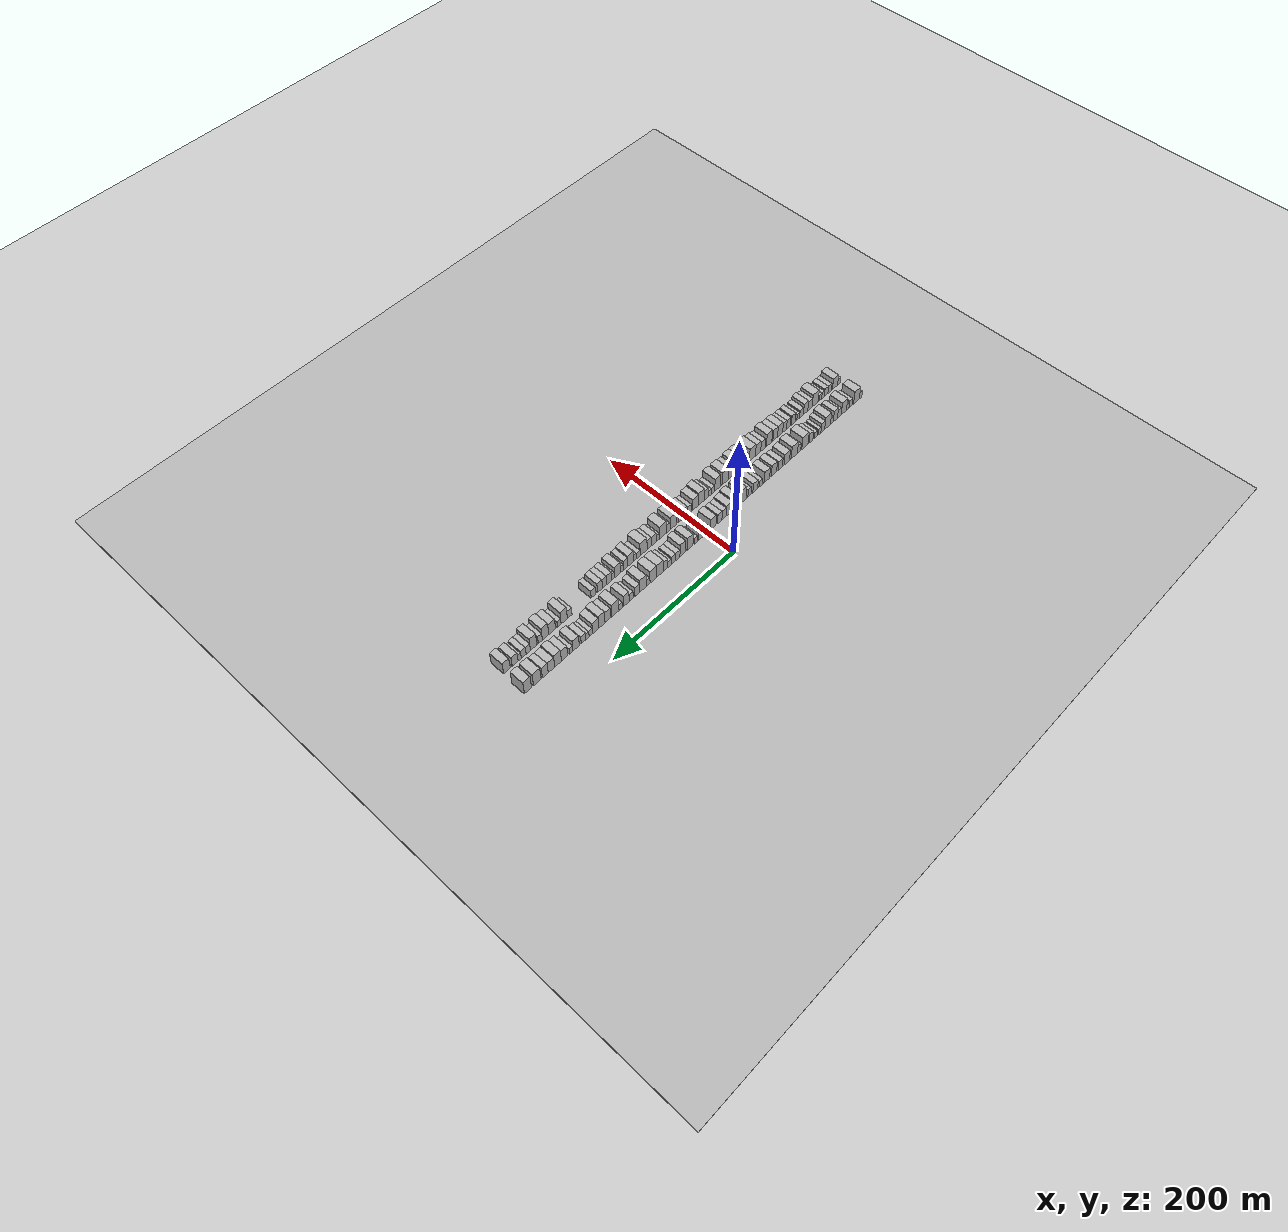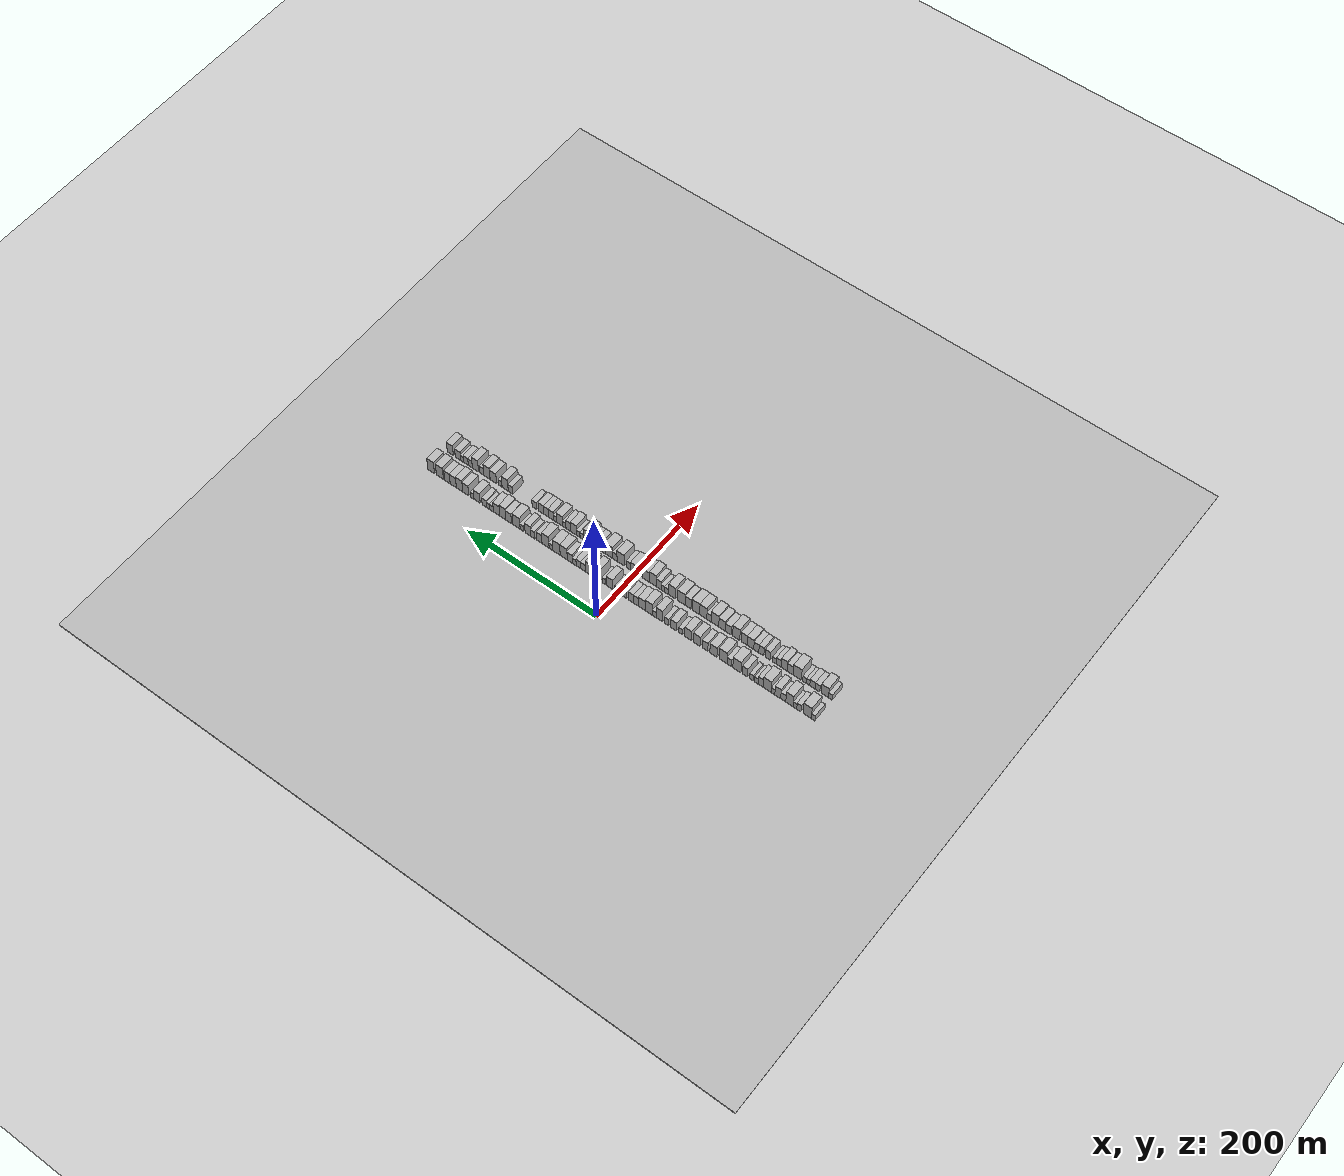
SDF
<?xml version="1.0" encoding="utf-8"?>

<sdf version="1.6">

   <world name="default">

      <gui fullscreen="0">

         <camera name="user_camera">

            <pose>-15 0 4.57585 0 0 0</pose>

            <view_controller>orbit</view_controller>

         </camera>

      </gui>

      <scene>

         <sky>

           <clouds>

             <speed>12</speed>

           </clouds>

         </sky>

         <ambient>0.4 0.4 0.4 1</ambient>

         <background>0.7 0.7 0.7 1</background>

         <shadows>1</shadows>

      </scene>

      <gravity>0 0 -9.8066</gravity>

      <magnetic_field>6e-06 2.3e-05 -4.2e-05</magnetic_field>

      <physics default="0" name="default_physics" type="ode">

         <ode>

            <solver>

               <type>quick</type>

               <iters>10</iters>

               <sor>1.0</sor>

               <use_dynamic_moi_rescaling>0</use_dynamic_moi_rescaling>

            </solver>

            <constraints>

               <cfm>0</cfm>

               <erp>0.2</erp>

               <contact_max_correcting_vel>100</contact_max_correcting_vel>

               <contact_surface_layer>0.001</contact_surface_layer>

            </constraints>

         </ode>

         <max_step_size>0.004</max_step_size>

         <real_time_factor>1</real_time_factor>

         <real_time_update_rate>250</real_time_update_rate>

      </physics>

      <light name="sun" type="directional">

         <cast_shadows>1</cast_shadows>

         <pose>0 0 10 0 0 0</pose>

         <diffuse>0.8 0.8 0.8 1</diffuse>

         <specular>0.2 0.2 0.2 1</specular>

         <attenuation>

            <range>1000</range>

            <constant>0.9</constant>

            <linear>0.01</linear>

            <quadratic>0.001</quadratic>

         </attenuation>

         <direction>-0.5 0.1 -0.9</direction>

      </light>

      <include>

         <name>ground_plane_1</name>

         <uri>model://HANNAS_ground_plane</uri>

         <pose>0 0 0  0 0 0</pose>

      </include>

      <include>

         <name>ground_plane_2</name>

         <uri>model://HANNAS_ground_plane</uri>

         <pose>100 0 0  0 0 0</pose>

      </include>

      <model name="building_1">

         <static>1</static>

         <pose frame="">50.0000 -287.3659 0 0.000000 0.000000 0.000000</pose>

         <link name="link">

            <pose frame="">0 0 6.00 0 0 0</pose>

            <collision name="collision">

               <geometry>

                  <box>

                     <size>20.0000 5.2683 12.0000</size>

                  </box>

               </geometry>

               <max_contacts>10</max_contacts>

               <surface>

                  <contact>

                     <ode/>

                  </contact>

                  <bounce/>

                  <friction>

                     <torsional>

                        <ode/>

                     </torsional>

                     <ode/>

                  </friction>

               </surface>

            </collision>

            <visual name="visual">

               <cast_shadows>0</cast_shadows>

               <geometry>

                  <box>

                     <size>20.0000 5.2683 12.0000</size>

                  </box>

               </geometry>

               <material>

                  <script>

                     <uri>model://HANNAS_wall/materials/scripts</uri>

                     <uri>model://HANNAS_wall/materials/textures</uri>

                     <name>vrc/HANNAS_wall</name>

                  </script>

               </material>

            </visual>

            <self_collide>0</self_collide>

            <enable_wind>0</enable_wind>

            <kinematic>0</kinematic>

         </link>

      </model>

      <model name="building_2">

         <static>1</static>

         <pose frame="">50.0000 -278.9402 0 0.000000 0.000000 0.000000</pose>

         <link name="link">

            <pose frame="">0 0 12.00 0 0 0</pose>

            <collision name="collision">

               <geometry>

                  <box>

                     <size>20.0000 11.5830 24.0000</size>

                  </box>

               </geometry>

               <max_contacts>10</max_contacts>

               <surface>

                  <contact>

                     <ode/>

                  </contact>

                  <bounce/>

                  <friction>

                     <torsional>

                        <ode/>

                     </torsional>

                     <ode/>

                  </friction>

               </surface>

            </collision>

            <visual name="visual">

               <cast_shadows>0</cast_shadows>

               <geometry>

                  <box>

                     <size>20.0000 11.5830 24.0000</size>

                  </box>

               </geometry>

               <material>

                  <script>

                     <uri>model://HANNAS_wall/materials/scripts</uri>

                     <uri>model://HANNAS_wall/materials/textures</uri>

                     <name>vrc/HANNAS_wall</name>

                  </script>

               </material>

            </visual>

            <self_collide>0</self_collide>

            <enable_wind>0</enable_wind>

            <kinematic>0</kinematic>

         </link>

      </model>

      <model name="building_3">

         <static>1</static>

         <pose frame="">50.0000 -267.0812 0 0.000000 0.000000 0.000000</pose>

         <link name="link">

            <pose frame="">0 0 7.50 0 0 0</pose>

            <collision name="collision">

               <geometry>

                  <box>

                     <size>20.0000 6.1351 15.0000</size>

                  </box>

               </geometry>

               <max_contacts>10</max_contacts>

               <surface>

                  <contact>

                     <ode/>

                  </contact>

                  <bounce/>

                  <friction>

                     <torsional>

                        <ode/>

                     </torsional>

                     <ode/>

                  </friction>

               </surface>

            </collision>

            <visual name="visual">

               <cast_shadows>0</cast_shadows>

               <geometry>

                  <box>

                     <size>20.0000 6.1351 15.0000</size>

                  </box>

               </geometry>

               <material>

                  <script>

                     <uri>model://HANNAS_wall/materials/scripts</uri>

                     <uri>model://HANNAS_wall/materials/textures</uri>

                     <name>vrc/HANNAS_wall</name>

                  </script>

               </material>

            </visual>

            <self_collide>0</self_collide>

            <enable_wind>0</enable_wind>

            <kinematic>0</kinematic>

         </link>

      </model>

      <model name="building_4">

         <static>1</static>

         <pose frame="">50.0000 -261.3872 0 0.000000 0.000000 0.000000</pose>

         <link name="link">

            <pose frame="">0 0 6.00 0 0 0</pose>

            <collision name="collision">

               <geometry>

                  <box>

                     <size>20.0000 5.2528 12.0000</size>

                  </box>

               </geometry>

               <max_contacts>10</max_contacts>

               <surface>

                  <contact>

                     <ode/>

                  </contact>

                  <bounce/>

                  <friction>

                     <torsional>

                        <ode/>

                     </torsional>

                     <ode/>

                  </friction>

               </surface>

            </collision>

            <visual name="visual">

               <cast_shadows>0</cast_shadows>

               <geometry>

                  <box>

                     <size>20.0000 5.2528 12.0000</size>

                  </box>

               </geometry>

               <material>

                  <script>

                     <uri>model://HANNAS_wall/materials/scripts</uri>

                     <uri>model://HANNAS_wall/materials/textures</uri>

                     <name>vrc/HANNAS_wall</name>

                  </script>

               </material>

            </visual>

            <self_collide>0</self_collide>

            <enable_wind>0</enable_wind>

            <kinematic>0</kinematic>

         </link>

      </model>

      <model name="building_5">

         <static>1</static>

         <pose frame="">50.0000 -253.4745 0 0.000000 0.000000 0.000000</pose>

         <link name="link">

            <pose frame="">0 0 12.00 0 0 0</pose>

            <collision name="collision">

               <geometry>

                  <box>

                     <size>20.0000 10.5725 24.0000</size>

                  </box>

               </geometry>

               <max_contacts>10</max_contacts>

               <surface>

                  <contact>

                     <ode/>

                  </contact>

                  <bounce/>

                  <friction>

                     <torsional>

                        <ode/>

                     </torsional>

                     <ode/>

                  </friction>

               </surface>

            </collision>

            <visual name="visual">

               <cast_shadows>0</cast_shadows>

               <geometry>

                  <box>

                     <size>20.0000 10.5725 24.0000</size>

                  </box>

               </geometry>

               <material>

                  <script>

                     <uri>model://HANNAS_wall/materials/scripts</uri>

                     <uri>model://HANNAS_wall/materials/textures</uri>

                     <name>vrc/HANNAS_wall</name>

                  </script>

               </material>

            </visual>

            <self_collide>0</self_collide>

            <enable_wind>0</enable_wind>

            <kinematic>0</kinematic>

         </link>

      </model>

      <model name="building_6">

         <static>1</static>

         <pose frame="">50.0000 -244.5200 0 0.000000 0.000000 0.000000</pose>

         <link name="link">

            <pose frame="">0 0 7.50 0 0 0</pose>

            <collision name="collision">

               <geometry>

                  <box>

                     <size>20.0000 7.3365 15.0000</size>

                  </box>

               </geometry>

               <max_contacts>10</max_contacts>

               <surface>

                  <contact>

                     <ode/>

                  </contact>

                  <bounce/>

                  <friction>

                     <torsional>

                        <ode/>

                     </torsional>

                     <ode/>

                  </friction>

               </surface>

            </collision>

            <visual name="visual">

               <cast_shadows>0</cast_shadows>

               <geometry>

                  <box>

                     <size>20.0000 7.3365 15.0000</size>

                  </box>

               </geometry>

               <material>

                  <script>

                     <uri>model://HANNAS_wall/materials/scripts</uri>

                     <uri>model://HANNAS_wall/materials/textures</uri>

                     <name>vrc/HANNAS_wall</name>

                  </script>

               </material>

            </visual>

            <self_collide>0</self_collide>

            <enable_wind>0</enable_wind>

            <kinematic>0</kinematic>

         </link>

      </model>

      <model name="building_7">

         <static>1</static>

         <pose frame="">50.0000 -236.6234 0 0.000000 0.000000 0.000000</pose>

         <link name="link">

            <pose frame="">0 0 10.50 0 0 0</pose>

            <collision name="collision">

               <geometry>

                  <box>

                     <size>20.0000 8.4568 21.0000</size>

                  </box>

               </geometry>

               <max_contacts>10</max_contacts>

               <surface>

                  <contact>

                     <ode/>

                  </contact>

                  <bounce/>

                  <friction>

                     <torsional>

                        <ode/>

                     </torsional>

                     <ode/>

                  </friction>

               </surface>

            </collision>

            <visual name="visual">

               <cast_shadows>0</cast_shadows>

               <geometry>

                  <box>

                     <size>20.0000 8.4568 21.0000</size>

                  </box>

               </geometry>

               <material>

                  <script>

                     <uri>model://HANNAS_wall/materials/scripts</uri>

                     <uri>model://HANNAS_wall/materials/textures</uri>

                     <name>vrc/HANNAS_wall</name>

                  </script>

               </material>

            </visual>

            <self_collide>0</self_collide>

            <enable_wind>0</enable_wind>

            <kinematic>0</kinematic>

         </link>

      </model>

      <model name="building_8">

         <static>1</static>

         <pose frame="">50.0000 -229.7621 0 0.000000 0.000000 0.000000</pose>

         <link name="link">

            <pose frame="">0 0 6.00 0 0 0</pose>

            <collision name="collision">

               <geometry>

                  <box>

                     <size>20.0000 5.2659 12.0000</size>

                  </box>

               </geometry>

               <max_contacts>10</max_contacts>

               <surface>

                  <contact>

                     <ode/>

                  </contact>

                  <bounce/>

                  <friction>

                     <torsional>

                        <ode/>

                     </torsional>

                     <ode/>

                  </friction>

               </surface>

            </collision>

            <visual name="visual">

               <cast_shadows>0</cast_shadows>

               <geometry>

                  <box>

                     <size>20.0000 5.2659 12.0000</size>

                  </box>

               </geometry>

               <material>

                  <script>

                     <uri>model://HANNAS_wall/materials/scripts</uri>

                     <uri>model://HANNAS_wall/materials/textures</uri>

                     <name>vrc/HANNAS_wall</name>

                  </script>

               </material>

            </visual>

            <self_collide>0</self_collide>

            <enable_wind>0</enable_wind>

            <kinematic>0</kinematic>

         </link>

      </model>

      <model name="building_9">

         <static>1</static>

         <pose frame="">50.0000 -221.4474 0 0.000000 0.000000 0.000000</pose>

         <link name="link">

            <pose frame="">0 0 12.00 0 0 0</pose>

            <collision name="collision">

               <geometry>

                  <box>

                     <size>20.0000 11.3634 24.0000</size>

                  </box>

               </geometry>

               <max_contacts>10</max_contacts>

               <surface>

                  <contact>

                     <ode/>

                  </contact>

                  <bounce/>

                  <friction>

                     <torsional>

                        <ode/>

                     </torsional>

                     <ode/>

                  </friction>

               </surface>

            </collision>

            <visual name="visual">

               <cast_shadows>0</cast_shadows>

               <geometry>

                  <box>

                     <size>20.0000 11.3634 24.0000</size>

                  </box>

               </geometry>

               <material>

                  <script>

                     <uri>model://HANNAS_wall/materials/scripts</uri>

                     <uri>model://HANNAS_wall/materials/textures</uri>

                     <name>vrc/HANNAS_wall</name>

                  </script>

               </material>

            </visual>

            <self_collide>0</self_collide>

            <enable_wind>0</enable_wind>

            <kinematic>0</kinematic>

         </link>

      </model>

      <model name="building_10">

         <static>1</static>

         <pose frame="">50.0000 -212.0919 0 0.000000 0.000000 0.000000</pose>

         <link name="link">

            <pose frame="">0 0 9.00 0 0 0</pose>

            <collision name="collision">

               <geometry>

                  <box>

                     <size>20.0000 7.3475 18.0000</size>

                  </box>

               </geometry>

               <max_contacts>10</max_contacts>

               <surface>

                  <contact>

                     <ode/>

                  </contact>

                  <bounce/>

                  <friction>

                     <torsional>

                        <ode/>

                     </torsional>

                     <ode/>

                  </friction>

               </surface>

            </collision>

            <visual name="visual">

               <cast_shadows>0</cast_shadows>

               <geometry>

                  <box>

                     <size>20.0000 7.3475 18.0000</size>

                  </box>

               </geometry>

               <material>

                  <script>

                     <uri>model://HANNAS_wall/materials/scripts</uri>

                     <uri>model://HANNAS_wall/materials/textures</uri>

                     <name>vrc/HANNAS_wall</name>

                  </script>

               </material>

            </visual>

            <self_collide>0</self_collide>

            <enable_wind>0</enable_wind>

            <kinematic>0</kinematic>

         </link>

      </model>

      <model name="building_11">

         <static>1</static>

         <pose frame="">50.0000 -205.8029 0 0.000000 0.000000 0.000000</pose>

         <link name="link">

            <pose frame="">0 0 6.00 0 0 0</pose>

            <collision name="collision">

               <geometry>

                  <box>

                     <size>20.0000 5.2305 12.0000</size>

                  </box>

               </geometry>

               <max_contacts>10</max_contacts>

               <surface>

                  <contact>

                     <ode/>

                  </contact>

                  <bounce/>

                  <friction>

                     <torsional>

                        <ode/>

                     </torsional>

                     <ode/>

                  </friction>

               </surface>

            </collision>

            <visual name="visual">

               <cast_shadows>0</cast_shadows>

               <geometry>

                  <box>

                     <size>20.0000 5.2305 12.0000</size>

                  </box>

               </geometry>

               <material>

                  <script>

                     <uri>model://HANNAS_wall/materials/scripts</uri>

                     <uri>model://HANNAS_wall/materials/textures</uri>

                     <name>vrc/HANNAS_wall</name>

                  </script>

               </material>

            </visual>

            <self_collide>0</self_collide>

            <enable_wind>0</enable_wind>

            <kinematic>0</kinematic>

         </link>

      </model>

      <model name="building_12">

         <static>1</static>

         <pose frame="">50.0000 -198.5033 0 0.000000 0.000000 0.000000</pose>

         <link name="link">

            <pose frame="">0 0 6.00 0 0 0</pose>

            <collision name="collision">

               <geometry>

                  <box>

                     <size>20.0000 5.3688 12.0000</size>

                  </box>

               </geometry>

               <max_contacts>10</max_contacts>

               <surface>

                  <contact>

                     <ode/>

                  </contact>

                  <bounce/>

                  <friction>

                     <torsional>

                        <ode/>

                     </torsional>

                     <ode/>

                  </friction>

               </surface>

            </collision>

            <visual name="visual">

               <cast_shadows>0</cast_shadows>

               <geometry>

                  <box>

                     <size>20.0000 5.3688 12.0000</size>

                  </box>

               </geometry>

               <material>

                  <script>

                     <uri>model://HANNAS_wall/materials/scripts</uri>

                     <uri>model://HANNAS_wall/materials/textures</uri>

                     <name>vrc/HANNAS_wall</name>

                  </script>

               </material>

            </visual>

            <self_collide>0</self_collide>

            <enable_wind>0</enable_wind>

            <kinematic>0</kinematic>

         </link>

      </model>

      <model name="building_13">

         <static>1</static>

         <pose frame="">50.0000 -189.1002 0 0.000000 0.000000 0.000000</pose>

         <link name="link">

            <pose frame="">0 0 9.00 0 0 0</pose>

            <collision name="collision">

               <geometry>

                  <box>

                     <size>20.0000 7.4374 18.0000</size>

                  </box>

               </geometry>

               <max_contacts>10</max_contacts>

               <surface>

                  <contact>

                     <ode/>

                  </contact>

                  <bounce/>

                  <friction>

                     <torsional>

                        <ode/>

                     </torsional>

                     <ode/>

                  </friction>

               </surface>

            </collision>

            <visual name="visual">

               <cast_shadows>0</cast_shadows>

               <geometry>

                  <box>

                     <size>20.0000 7.4374 18.0000</size>

                  </box>

               </geometry>

               <material>

                  <script>

                     <uri>model://HANNAS_wall/materials/scripts</uri>

                     <uri>model://HANNAS_wall/materials/textures</uri>

                     <name>vrc/HANNAS_wall</name>

                  </script>

               </material>

            </visual>

            <self_collide>0</self_collide>

            <enable_wind>0</enable_wind>

            <kinematic>0</kinematic>

         </link>

      </model>

      <model name="building_14">

         <static>1</static>

         <pose frame="">50.0000 -177.4174 0 0.000000 0.000000 0.000000</pose>

         <link name="link">

            <pose frame="">0 0 12.00 0 0 0</pose>

            <collision name="collision">

               <geometry>

                  <box>

                     <size>20.0000 11.9281 24.0000</size>

                  </box>

               </geometry>

               <max_contacts>10</max_contacts>

               <surface>

                  <contact>

                     <ode/>

                  </contact>

                  <bounce/>

                  <friction>

                     <torsional>

                        <ode/>

                     </torsional>

                     <ode/>

                  </friction>

               </surface>

            </collision>

            <visual name="visual">

               <cast_shadows>0</cast_shadows>

               <geometry>

                  <box>

                     <size>20.0000 11.9281 24.0000</size>

                  </box>

               </geometry>

               <material>

                  <script>

                     <uri>model://HANNAS_wall/materials/scripts</uri>

                     <uri>model://HANNAS_wall/materials/textures</uri>

                     <name>vrc/HANNAS_wall</name>

                  </script>

               </material>

            </visual>

            <self_collide>0</self_collide>

            <enable_wind>0</enable_wind>

            <kinematic>0</kinematic>

         </link>

      </model>

      <model name="building_15">

         <static>1</static>

         <pose frame="">50.0000 -166.1783 0 0.000000 0.000000 0.000000</pose>

         <link name="link">

            <pose frame="">0 0 7.50 0 0 0</pose>

            <collision name="collision">

               <geometry>

                  <box>

                     <size>20.0000 6.5502 15.0000</size>

                  </box>

               </geometry>

               <max_contacts>10</max_contacts>

               <surface>

                  <contact>

                     <ode/>

                  </contact>

                  <bounce/>

                  <friction>

                     <torsional>

                        <ode/>

                     </torsional>

                     <ode/>

                  </friction>

               </surface>

            </collision>

            <visual name="visual">

               <cast_shadows>0</cast_shadows>

               <geometry>

                  <box>

                     <size>20.0000 6.5502 15.0000</size>

                  </box>

               </geometry>

               <material>

                  <script>

                     <uri>model://HANNAS_wall/materials/scripts</uri>

                     <uri>model://HANNAS_wall/materials/textures</uri>

                     <name>vrc/HANNAS_wall</name>

                  </script>

               </material>

            </visual>

            <self_collide>0</self_collide>

            <enable_wind>0</enable_wind>

            <kinematic>0</kinematic>

         </link>

      </model>

      <model name="building_16">

         <static>1</static>

         <pose frame="">50.0000 -157.0334 0 0.000000 0.000000 0.000000</pose>

         <link name="link">

            <pose frame="">0 0 12.00 0 0 0</pose>

            <collision name="collision">

               <geometry>

                  <box>

                     <size>20.0000 11.7396 24.0000</size>

                  </box>

               </geometry>

               <max_contacts>10</max_contacts>

               <surface>

                  <contact>

                     <ode/>

                  </contact>

                  <bounce/>

                  <friction>

                     <torsional>

                        <ode/>

                     </torsional>

                     <ode/>

                  </friction>

               </surface>

            </collision>

            <visual name="visual">

               <cast_shadows>0</cast_shadows>

               <geometry>

                  <box>

                     <size>20.0000 11.7396 24.0000</size>

                  </box>

               </geometry>

               <material>

                  <script>

                     <uri>model://HANNAS_wall/materials/scripts</uri>

                     <uri>model://HANNAS_wall/materials/textures</uri>

                     <name>vrc/HANNAS_wall</name>

                  </script>

               </material>

            </visual>

            <self_collide>0</self_collide>

            <enable_wind>0</enable_wind>

            <kinematic>0</kinematic>

         </link>

      </model>

      <model name="building_17">

         <static>1</static>

         <pose frame="">50.0000 -142.9570 0 0.000000 0.000000 0.000000</pose>

         <link name="link">

            <pose frame="">0 0 10.50 0 0 0</pose>

            <collision name="collision">

               <geometry>

                  <box>

                     <size>20.0000 10.4133 21.0000</size>

                  </box>

               </geometry>

               <max_contacts>10</max_contacts>

               <surface>

                  <contact>

                     <ode/>

                  </contact>

                  <bounce/>

                  <friction>

                     <torsional>

                        <ode/>

                     </torsional>

                     <ode/>

                  </friction>

               </surface>

            </collision>

            <visual name="visual">

               <cast_shadows>0</cast_shadows>

               <geometry>

                  <box>

                     <size>20.0000 10.4133 21.0000</size>

                  </box>

               </geometry>

               <material>

                  <script>

                     <uri>model://HANNAS_wall/materials/scripts</uri>

                     <uri>model://HANNAS_wall/materials/textures</uri>

                     <name>vrc/HANNAS_wall</name>

                  </script>

               </material>

            </visual>

            <self_collide>0</self_collide>

            <enable_wind>0</enable_wind>

            <kinematic>0</kinematic>

         </link>

      </model>

      <model name="building_18">

         <static>1</static>

         <pose frame="">50.0000 -130.7641 0 0.000000 0.000000 0.000000</pose>

         <link name="link">

            <pose frame="">0 0 9.00 0 0 0</pose>

            <collision name="collision">

               <geometry>

                  <box>

                     <size>20.0000 7.9725 18.0000</size>

                  </box>

               </geometry>

               <max_contacts>10</max_contacts>

               <surface>

                  <contact>

                     <ode/>

                  </contact>

                  <bounce/>

                  <friction>

                     <torsional>

                        <ode/>

                     </torsional>

                     <ode/>

                  </friction>

               </surface>

            </collision>

            <visual name="visual">

               <cast_shadows>0</cast_shadows>

               <geometry>

                  <box>

                     <size>20.0000 7.9725 18.0000</size>

                  </box>

               </geometry>

               <material>

                  <script>

                     <uri>model://HANNAS_wall/materials/scripts</uri>

                     <uri>model://HANNAS_wall/materials/textures</uri>

                     <name>vrc/HANNAS_wall</name>

                  </script>

               </material>

            </visual>

            <self_collide>0</self_collide>

            <enable_wind>0</enable_wind>

            <kinematic>0</kinematic>

         </link>

      </model>

      <model name="building_19">

         <static>1</static>

         <pose frame="">50.0000 -118.8016 0 0.000000 0.000000 0.000000</pose>

         <link name="link">

            <pose frame="">0 0 10.50 0 0 0</pose>

            <collision name="collision">

               <geometry>

                  <box>

                     <size>20.0000 9.9525 21.0000</size>

                  </box>

               </geometry>

               <max_contacts>10</max_contacts>

               <surface>

                  <contact>

                     <ode/>

                  </contact>

                  <bounce/>

                  <friction>

                     <torsional>

                        <ode/>

                     </torsional>

                     <ode/>

                  </friction>

               </surface>

            </collision>

            <visual name="visual">

               <cast_shadows>0</cast_shadows>

               <geometry>

                  <box>

                     <size>20.0000 9.9525 21.0000</size>

                  </box>

               </geometry>

               <material>

                  <script>

                     <uri>model://HANNAS_wall/materials/scripts</uri>

                     <uri>model://HANNAS_wall/materials/textures</uri>

                     <name>vrc/HANNAS_wall</name>

                  </script>

               </material>

            </visual>

            <self_collide>0</self_collide>

            <enable_wind>0</enable_wind>

            <kinematic>0</kinematic>

         </link>

      </model>

      <model name="building_20">

         <static>1</static>

         <pose frame="">50.0000 -105.7524 0 0.000000 0.000000 0.000000</pose>

         <link name="link">

            <pose frame="">0 0 10.50 0 0 0</pose>

            <collision name="collision">

               <geometry>

                  <box>

                     <size>20.0000 10.1458 21.0000</size>

                  </box>

               </geometry>

               <max_contacts>10</max_contacts>

               <surface>

                  <contact>

                     <ode/>

                  </contact>

                  <bounce/>

                  <friction>

                     <torsional>

                        <ode/>

                     </torsional>

                     <ode/>

                  </friction>

               </surface>

            </collision>

            <visual name="visual">

               <cast_shadows>0</cast_shadows>

               <geometry>

                  <box>

                     <size>20.0000 10.1458 21.0000</size>

                  </box>

               </geometry>

               <material>

                  <script>

                     <uri>model://HANNAS_wall/materials/scripts</uri>

                     <uri>model://HANNAS_wall/materials/textures</uri>

                     <name>vrc/HANNAS_wall</name>

                  </script>

               </material>

            </visual>

            <self_collide>0</self_collide>

            <enable_wind>0</enable_wind>

            <kinematic>0</kinematic>

         </link>

      </model>

      <model name="building_21">

         <static>1</static>

         <pose frame="">50.0000 -94.7142 0 0.000000 0.000000 0.000000</pose>

         <link name="link">

            <pose frame="">0 0 6.00 0 0 0</pose>

            <collision name="collision">

               <geometry>

                  <box>

                     <size>20.0000 5.9307 12.0000</size>

                  </box>

               </geometry>

               <max_contacts>10</max_contacts>

               <surface>

                  <contact>

                     <ode/>

                  </contact>

                  <bounce/>

                  <friction>

                     <torsional>

                        <ode/>

                     </torsional>

                     <ode/>

                  </friction>

               </surface>

            </collision>

            <visual name="visual">

               <cast_shadows>0</cast_shadows>

               <geometry>

                  <box>

                     <size>20.0000 5.9307 12.0000</size>

                  </box>

               </geometry>

               <material>

                  <script>

                     <uri>model://HANNAS_wall/materials/scripts</uri>

                     <uri>model://HANNAS_wall/materials/textures</uri>

                     <name>vrc/HANNAS_wall</name>

                  </script>

               </material>

            </visual>

            <self_collide>0</self_collide>

            <enable_wind>0</enable_wind>

            <kinematic>0</kinematic>

         </link>

      </model>

      <model name="building_22">

         <static>1</static>

         <pose frame="">50.0000 -84.2666 0 0.000000 0.000000 0.000000</pose>

         <link name="link">

            <pose frame="">0 0 9.00 0 0 0</pose>

            <collision name="collision">

               <geometry>

                  <box>

                     <size>20.0000 8.9644 18.0000</size>

                  </box>

               </geometry>

               <max_contacts>10</max_contacts>

               <surface>

                  <contact>

                     <ode/>

                  </contact>

                  <bounce/>

                  <friction>

                     <torsional>

                        <ode/>

                     </torsional>

                     <ode/>

                  </friction>

               </surface>

            </collision>

            <visual name="visual">

               <cast_shadows>0</cast_shadows>

               <geometry>

                  <box>

                     <size>20.0000 8.9644 18.0000</size>

                  </box>

               </geometry>

               <material>

                  <script>

                     <uri>model://HANNAS_wall/materials/scripts</uri>

                     <uri>model://HANNAS_wall/materials/textures</uri>

                     <name>vrc/HANNAS_wall</name>

                  </script>

               </material>

            </visual>

            <self_collide>0</self_collide>

            <enable_wind>0</enable_wind>

            <kinematic>0</kinematic>

         </link>

      </model>

      <model name="building_23">

         <static>1</static>

         <pose frame="">50.0000 -73.7801 0 0.000000 0.000000 0.000000</pose>

         <link name="link">

            <pose frame="">0 0 7.50 0 0 0</pose>

            <collision name="collision">

               <geometry>

                  <box>

                     <size>20.0000 6.0086 15.0000</size>

                  </box>

               </geometry>

               <max_contacts>10</max_contacts>

               <surface>

                  <contact>

                     <ode/>

                  </contact>

                  <bounce/>

                  <friction>

                     <torsional>

                        <ode/>

                     </torsional>

                     <ode/>

                  </friction>

               </surface>

            </collision>

            <visual name="visual">

               <cast_shadows>0</cast_shadows>

               <geometry>

                  <box>

                     <size>20.0000 6.0086 15.0000</size>

                  </box>

               </geometry>

               <material>

                  <script>

                     <uri>model://HANNAS_wall/materials/scripts</uri>

                     <uri>model://HANNAS_wall/materials/textures</uri>

                     <name>vrc/HANNAS_wall</name>

                  </script>

               </material>

            </visual>

            <self_collide>0</self_collide>

            <enable_wind>0</enable_wind>

            <kinematic>0</kinematic>

         </link>

      </model>

      <model name="building_24">

         <static>1</static>

         <pose frame="">50.0000 -62.9027 0 0.000000 0.000000 0.000000</pose>

         <link name="link">

            <pose frame="">0 0 12.00 0 0 0</pose>

            <collision name="collision">

               <geometry>

                  <box>

                     <size>20.0000 9.7461 24.0000</size>

                  </box>

               </geometry>

               <max_contacts>10</max_contacts>

               <surface>

                  <contact>

                     <ode/>

                  </contact>

                  <bounce/>

                  <friction>

                     <torsional>

                        <ode/>

                     </torsional>

                     <ode/>

                  </friction>

               </surface>

            </collision>

            <visual name="visual">

               <cast_shadows>0</cast_shadows>

               <geometry>

                  <box>

                     <size>20.0000 9.7461 24.0000</size>

                  </box>

               </geometry>

               <material>

                  <script>

                     <uri>model://HANNAS_wall/materials/scripts</uri>

                     <uri>model://HANNAS_wall/materials/textures</uri>

                     <name>vrc/HANNAS_wall</name>

                  </script>

               </material>

            </visual>

            <self_collide>0</self_collide>

            <enable_wind>0</enable_wind>

            <kinematic>0</kinematic>

         </link>

      </model>

      <model name="building_25">

         <static>1</static>

         <pose frame="">50.0000 -55.1246 0 0.000000 0.000000 0.000000</pose>

         <link name="link">

            <pose frame="">0 0 6.00 0 0 0</pose>

            <collision name="collision">

               <geometry>

                  <box>

                     <size>20.0000 5.8101 12.0000</size>

                  </box>

               </geometry>

               <max_contacts>10</max_contacts>

               <surface>

                  <contact>

                     <ode/>

                  </contact>

                  <bounce/>

                  <friction>

                     <torsional>

                        <ode/>

                     </torsional>

                     <ode/>

                  </friction>

               </surface>

            </collision>

            <visual name="visual">

               <cast_shadows>0</cast_shadows>

               <geometry>

                  <box>

                     <size>20.0000 5.8101 12.0000</size>

                  </box>

               </geometry>

               <material>

                  <script>

                     <uri>model://HANNAS_wall/materials/scripts</uri>

                     <uri>model://HANNAS_wall/materials/textures</uri>

                     <name>vrc/HANNAS_wall</name>

                  </script>

               </material>

            </visual>

            <self_collide>0</self_collide>

            <enable_wind>0</enable_wind>

            <kinematic>0</kinematic>

         </link>

      </model>

      <model name="building_26">

         <static>1</static>

         <pose frame="">50.0000 -46.8918 0 0.000000 0.000000 0.000000</pose>

         <link name="link">

            <pose frame="">0 0 12.00 0 0 0</pose>

            <collision name="collision">

               <geometry>

                  <box>

                     <size>20.0000 10.6555 24.0000</size>

                  </box>

               </geometry>

               <max_contacts>10</max_contacts>

               <surface>

                  <contact>

                     <ode/>

                  </contact>

                  <bounce/>

                  <friction>

                     <torsional>

                        <ode/>

                     </torsional>

                     <ode/>

                  </friction>

               </surface>

            </collision>

            <visual name="visual">

               <cast_shadows>0</cast_shadows>

               <geometry>

                  <box>

                     <size>20.0000 10.6555 24.0000</size>

                  </box>

               </geometry>

               <material>

                  <script>

                     <uri>model://HANNAS_wall/materials/scripts</uri>

                     <uri>model://HANNAS_wall/materials/textures</uri>

                     <name>vrc/HANNAS_wall</name>

                  </script>

               </material>

            </visual>

            <self_collide>0</self_collide>

            <enable_wind>0</enable_wind>

            <kinematic>0</kinematic>

         </link>

      </model>

      <model name="building_27">

         <static>1</static>

         <pose frame="">50.0000 -36.4208 0 0.000000 0.000000 0.000000</pose>

         <link name="link">

            <pose frame="">0 0 10.50 0 0 0</pose>

            <collision name="collision">

               <geometry>

                  <box>

                     <size>20.0000 10.2866 21.0000</size>

                  </box>

               </geometry>

               <max_contacts>10</max_contacts>

               <surface>

                  <contact>

                     <ode/>

                  </contact>

                  <bounce/>

                  <friction>

                     <torsional>

                        <ode/>

                     </torsional>

                     <ode/>

                  </friction>

               </surface>

            </collision>

            <visual name="visual">

               <cast_shadows>0</cast_shadows>

               <geometry>

                  <box>

                     <size>20.0000 10.2866 21.0000</size>

                  </box>

               </geometry>

               <material>

                  <script>

                     <uri>model://HANNAS_wall/materials/scripts</uri>

                     <uri>model://HANNAS_wall/materials/textures</uri>

                     <name>vrc/HANNAS_wall</name>

                  </script>

               </material>

            </visual>

            <self_collide>0</self_collide>

            <enable_wind>0</enable_wind>

            <kinematic>0</kinematic>

         </link>

      </model>

      <model name="building_28">

         <static>1</static>

         <pose frame="">50.0000 -27.6538 0 0.000000 0.000000 0.000000</pose>

         <link name="link">

            <pose frame="">0 0 9.00 0 0 0</pose>

            <collision name="collision">

               <geometry>

                  <box>

                     <size>20.0000 7.2474 18.0000</size>

                  </box>

               </geometry>

               <max_contacts>10</max_contacts>

               <surface>

                  <contact>

                     <ode/>

                  </contact>

                  <bounce/>

                  <friction>

                     <torsional>

                        <ode/>

                     </torsional>

                     <ode/>

                  </friction>

               </surface>

            </collision>

            <visual name="visual">

               <cast_shadows>0</cast_shadows>

               <geometry>

                  <box>

                     <size>20.0000 7.2474 18.0000</size>

                  </box>

               </geometry>

               <material>

                  <script>

                     <uri>model://HANNAS_wall/materials/scripts</uri>

                     <uri>model://HANNAS_wall/materials/textures</uri>

                     <name>vrc/HANNAS_wall</name>

                  </script>

               </material>

            </visual>

            <self_collide>0</self_collide>

            <enable_wind>0</enable_wind>

            <kinematic>0</kinematic>

         </link>

      </model>

      <model name="building_29">

         <static>1</static>

         <pose frame="">50.0000 -20.2524 0 0.000000 0.000000 0.000000</pose>

         <link name="link">

            <pose frame="">0 0 9.00 0 0 0</pose>

            <collision name="collision">

               <geometry>

                  <box>

                     <size>20.0000 7.5553 18.0000</size>

                  </box>

               </geometry>

               <max_contacts>10</max_contacts>

               <surface>

                  <contact>

                     <ode/>

                  </contact>

                  <bounce/>

                  <friction>

                     <torsional>

                        <ode/>

                     </torsional>

                     <ode/>

                  </friction>

               </surface>

            </collision>

            <visual name="visual">

               <cast_shadows>0</cast_shadows>

               <geometry>

                  <box>

                     <size>20.0000 7.5553 18.0000</size>

                  </box>

               </geometry>

               <material>

                  <script>

                     <uri>model://HANNAS_wall/materials/scripts</uri>

                     <uri>model://HANNAS_wall/materials/textures</uri>

                     <name>vrc/HANNAS_wall</name>

                  </script>

               </material>

            </visual>

            <self_collide>0</self_collide>

            <enable_wind>0</enable_wind>

            <kinematic>0</kinematic>

         </link>

      </model>

      <model name="building_30">

         <static>1</static>

         <pose frame="">50.0000 -8.5156 0 0.000000 0.000000 0.000000</pose>

         <link name="link">

            <pose frame="">0 0 10.50 0 0 0</pose>

            <collision name="collision">

               <geometry>

                  <box>

                     <size>20.0000 9.9183 21.0000</size>

                  </box>

               </geometry>

               <max_contacts>10</max_contacts>

               <surface>

                  <contact>

                     <ode/>

                  </contact>

                  <bounce/>

                  <friction>

                     <torsional>

                        <ode/>

                     </torsional>

                     <ode/>

                  </friction>

               </surface>

            </collision>

            <visual name="visual">

               <cast_shadows>0</cast_shadows>

               <geometry>

                  <box>

                     <size>20.0000 9.9183 21.0000</size>

                  </box>

               </geometry>

               <material>

                  <script>

                     <uri>model://HANNAS_wall/materials/scripts</uri>

                     <uri>model://HANNAS_wall/materials/textures</uri>

                     <name>vrc/HANNAS_wall</name>

                  </script>

               </material>

            </visual>

            <self_collide>0</self_collide>

            <enable_wind>0</enable_wind>

            <kinematic>0</kinematic>

         </link>

      </model>

      <model name="building_31">

         <static>1</static>

         <pose frame="">50.0000 1.8954 0 0.000000 0.000000 0.000000</pose>

         <link name="link">

            <pose frame="">0 0 6.00 0 0 0</pose>

            <collision name="collision">

               <geometry>

                  <box>

                     <size>20.0000 4.9037 12.0000</size>

                  </box>

               </geometry>

               <max_contacts>10</max_contacts>

               <surface>

                  <contact>

                     <ode/>

                  </contact>

                  <bounce/>

                  <friction>

                     <torsional>

                        <ode/>

                     </torsional>

                     <ode/>

                  </friction>

               </surface>

            </collision>

            <visual name="visual">

               <cast_shadows>0</cast_shadows>

               <geometry>

                  <box>

                     <size>20.0000 4.9037 12.0000</size>

                  </box>

               </geometry>

               <material>

                  <script>

                     <uri>model://HANNAS_wall/materials/scripts</uri>

                     <uri>model://HANNAS_wall/materials/textures</uri>

                     <name>vrc/HANNAS_wall</name>

                  </script>

               </material>

            </visual>

            <self_collide>0</self_collide>

            <enable_wind>0</enable_wind>

            <kinematic>0</kinematic>

         </link>

      </model>

      <model name="building_32">

         <static>1</static>

         <pose frame="">50.0000 12.0339 0 0.000000 0.000000 0.000000</pose>

         <link name="link">

            <pose frame="">0 0 10.50 0 0 0</pose>

            <collision name="collision">

               <geometry>

                  <box>

                     <size>20.0000 9.3732 21.0000</size>

                  </box>

               </geometry>

               <max_contacts>10</max_contacts>

               <surface>

                  <contact>

                     <ode/>

                  </contact>

                  <bounce/>

                  <friction>

                     <torsional>

                        <ode/>

                     </torsional>

                     <ode/>

                  </friction>

               </surface>

            </collision>

            <visual name="visual">

               <cast_shadows>0</cast_shadows>

               <geometry>

                  <box>

                     <size>20.0000 9.3732 21.0000</size>

                  </box>

               </geometry>

               <material>

                  <script>

                     <uri>model://HANNAS_wall/materials/scripts</uri>

                     <uri>model://HANNAS_wall/materials/textures</uri>

                     <name>vrc/HANNAS_wall</name>

                  </script>

               </material>

            </visual>

            <self_collide>0</self_collide>

            <enable_wind>0</enable_wind>

            <kinematic>0</kinematic>

         </link>

      </model>

      <model name="building_33">

         <static>1</static>

         <pose frame="">50.0000 21.2638 0 0.000000 0.000000 0.000000</pose>

         <link name="link">

            <pose frame="">0 0 6.00 0 0 0</pose>

            <collision name="collision">

               <geometry>

                  <box>

                     <size>20.0000 5.0866 12.0000</size>

                  </box>

               </geometry>

               <max_contacts>10</max_contacts>

               <surface>

                  <contact>

                     <ode/>

                  </contact>

                  <bounce/>

                  <friction>

                     <torsional>

                        <ode/>

                     </torsional>

                     <ode/>

                  </friction>

               </surface>

            </collision>

            <visual name="visual">

               <cast_shadows>0</cast_shadows>

               <geometry>

                  <box>

                     <size>20.0000 5.0866 12.0000</size>

                  </box>

               </geometry>

               <material>

                  <script>

                     <uri>model://HANNAS_wall/materials/scripts</uri>

                     <uri>model://HANNAS_wall/materials/textures</uri>

                     <name>vrc/HANNAS_wall</name>

                  </script>

               </material>

            </visual>

            <self_collide>0</self_collide>

            <enable_wind>0</enable_wind>

            <kinematic>0</kinematic>

         </link>

      </model>

      <model name="building_34">

         <static>1</static>

         <pose frame="">50.0000 31.6727 0 0.000000 0.000000 0.000000</pose>

         <link name="link">

            <pose frame="">0 0 12.00 0 0 0</pose>

            <collision name="collision">

               <geometry>

                  <box>

                     <size>20.0000 9.7312 24.0000</size>

                  </box>

               </geometry>

               <max_contacts>10</max_contacts>

               <surface>

                  <contact>

                     <ode/>

                  </contact>

                  <bounce/>

                  <friction>

                     <torsional>

                        <ode/>

                     </torsional>

                     <ode/>

                  </friction>

               </surface>

            </collision>

            <visual name="visual">

               <cast_shadows>0</cast_shadows>

               <geometry>

                  <box>

                     <size>20.0000 9.7312 24.0000</size>

                  </box>

               </geometry>

               <material>

                  <script>

                     <uri>model://HANNAS_wall/materials/scripts</uri>

                     <uri>model://HANNAS_wall/materials/textures</uri>

                     <name>vrc/HANNAS_wall</name>

                  </script>

               </material>

            </visual>

            <self_collide>0</self_collide>

            <enable_wind>0</enable_wind>

            <kinematic>0</kinematic>

         </link>

      </model>

      <model name="building_35">

         <static>1</static>

         <pose frame="">50.0000 44.3446 0 0.000000 0.000000 0.000000</pose>

         <link name="link">

            <pose frame="">0 0 12.00 0 0 0</pose>

            <collision name="collision">

               <geometry>

                  <box>

                     <size>20.0000 9.6127 24.0000</size>

                  </box>

               </geometry>

               <max_contacts>10</max_contacts>

               <surface>

                  <contact>

                     <ode/>

                  </contact>

                  <bounce/>

                  <friction>

                     <torsional>

                        <ode/>

                     </torsional>

                     <ode/>

                  </friction>

               </surface>

            </collision>

            <visual name="visual">

               <cast_shadows>0</cast_shadows>

               <geometry>

                  <box>

                     <size>20.0000 9.6127 24.0000</size>

                  </box>

               </geometry>

               <material>

                  <script>

                     <uri>model://HANNAS_wall/materials/scripts</uri>

                     <uri>model://HANNAS_wall/materials/textures</uri>

                     <name>vrc/HANNAS_wall</name>

                  </script>

               </material>

            </visual>

            <self_collide>0</self_collide>

            <enable_wind>0</enable_wind>

            <kinematic>0</kinematic>

         </link>

      </model>

      <model name="building_36">

         <static>1</static>

         <pose frame="">50.0000 52.7396 0 0.000000 0.000000 0.000000</pose>

         <link name="link">

            <pose frame="">0 0 7.50 0 0 0</pose>

            <collision name="collision">

               <geometry>

                  <box>

                     <size>20.0000 7.1774 15.0000</size>

                  </box>

               </geometry>

               <max_contacts>10</max_contacts>

               <surface>

                  <contact>

                     <ode/>

                  </contact>

                  <bounce/>

                  <friction>

                     <torsional>

                        <ode/>

                     </torsional>

                     <ode/>

                  </friction>

               </surface>

            </collision>

            <visual name="visual">

               <cast_shadows>0</cast_shadows>

               <geometry>

                  <box>

                     <size>20.0000 7.1774 15.0000</size>

                  </box>

               </geometry>

               <material>

                  <script>

                     <uri>model://HANNAS_wall/materials/scripts</uri>

                     <uri>model://HANNAS_wall/materials/textures</uri>

                     <name>vrc/HANNAS_wall</name>

                  </script>

               </material>

            </visual>

            <self_collide>0</self_collide>

            <enable_wind>0</enable_wind>

            <kinematic>0</kinematic>

         </link>

      </model>

      <model name="building_37">

         <static>1</static>

         <pose frame="">50.0000 59.9838 0 0.000000 0.000000 0.000000</pose>

         <link name="link">

            <pose frame="">0 0 7.50 0 0 0</pose>

            <collision name="collision">

               <geometry>

                  <box>

                     <size>20.0000 7.3109 15.0000</size>

                  </box>

               </geometry>

               <max_contacts>10</max_contacts>

               <surface>

                  <contact>

                     <ode/>

                  </contact>

                  <bounce/>

                  <friction>

                     <torsional>

                        <ode/>

                     </torsional>

                     <ode/>

                  </friction>

               </surface>

            </collision>

            <visual name="visual">

               <cast_shadows>0</cast_shadows>

               <geometry>

                  <box>

                     <size>20.0000 7.3109 15.0000</size>

                  </box>

               </geometry>

               <material>

                  <script>

                     <uri>model://HANNAS_wall/materials/scripts</uri>

                     <uri>model://HANNAS_wall/materials/textures</uri>

                     <name>vrc/HANNAS_wall</name>

                  </script>

               </material>

            </visual>

            <self_collide>0</self_collide>

            <enable_wind>0</enable_wind>

            <kinematic>0</kinematic>

         </link>

      </model>

      <model name="building_38">

         <static>1</static>

         <pose frame="">50.0000 66.6029 0 0.000000 0.000000 0.000000</pose>

         <link name="link">

            <pose frame="">0 0 6.00 0 0 0</pose>

            <collision name="collision">

               <geometry>

                  <box>

                     <size>20.0000 5.9274 12.0000</size>

                  </box>

               </geometry>

               <max_contacts>10</max_contacts>

               <surface>

                  <contact>

                     <ode/>

                  </contact>

                  <bounce/>

                  <friction>

                     <torsional>

                        <ode/>

                     </torsional>

                     <ode/>

                  </friction>

               </surface>

            </collision>

            <visual name="visual">

               <cast_shadows>0</cast_shadows>

               <geometry>

                  <box>

                     <size>20.0000 5.9274 12.0000</size>

                  </box>

               </geometry>

               <material>

                  <script>

                     <uri>model://HANNAS_wall/materials/scripts</uri>

                     <uri>model://HANNAS_wall/materials/textures</uri>

                     <name>vrc/HANNAS_wall</name>

                  </script>

               </material>

            </visual>

            <self_collide>0</self_collide>

            <enable_wind>0</enable_wind>

            <kinematic>0</kinematic>

         </link>

      </model>

      <model name="building_39">

         <static>1</static>

         <pose frame="">50.0000 73.4541 0 0.000000 0.000000 0.000000</pose>

         <link name="link">

            <pose frame="">0 0 9.00 0 0 0</pose>

            <collision name="collision">

               <geometry>

                  <box>

                     <size>20.0000 7.7750 18.0000</size>

                  </box>

               </geometry>

               <max_contacts>10</max_contacts>

               <surface>

                  <contact>

                     <ode/>

                  </contact>

                  <bounce/>

                  <friction>

                     <torsional>

                        <ode/>

                     </torsional>

                     <ode/>

                  </friction>

               </surface>

            </collision>

            <visual name="visual">

               <cast_shadows>0</cast_shadows>

               <geometry>

                  <box>

                     <size>20.0000 7.7750 18.0000</size>

                  </box>

               </geometry>

               <material>

                  <script>

                     <uri>model://HANNAS_wall/materials/scripts</uri>

                     <uri>model://HANNAS_wall/materials/textures</uri>

                     <name>vrc/HANNAS_wall</name>

                  </script>

               </material>

            </visual>

            <self_collide>0</self_collide>

            <enable_wind>0</enable_wind>

            <kinematic>0</kinematic>

         </link>

      </model>

      <model name="building_40">

         <static>1</static>

         <pose frame="">50.0000 82.8072 0 0.000000 0.000000 0.000000</pose>

         <link name="link">

            <pose frame="">0 0 12.00 0 0 0</pose>

            <collision name="collision">

               <geometry>

                  <box>

                     <size>20.0000 10.9311 24.0000</size>

                  </box>

               </geometry>

               <max_contacts>10</max_contacts>

               <surface>

                  <contact>

                     <ode/>

                  </contact>

                  <bounce/>

                  <friction>

                     <torsional>

                        <ode/>

                     </torsional>

                     <ode/>

                  </friction>

               </surface>

            </collision>

            <visual name="visual">

               <cast_shadows>0</cast_shadows>

               <geometry>

                  <box>

                     <size>20.0000 10.9311 24.0000</size>

                  </box>

               </geometry>

               <material>

                  <script>

                     <uri>model://HANNAS_wall/materials/scripts</uri>

                     <uri>model://HANNAS_wall/materials/textures</uri>

                     <name>vrc/HANNAS_wall</name>

                  </script>

               </material>

            </visual>

            <self_collide>0</self_collide>

            <enable_wind>0</enable_wind>

            <kinematic>0</kinematic>

         </link>

      </model>

      <model name="building_41">

         <static>1</static>

         <pose frame="">50.0000 93.9608 0 0.000000 0.000000 0.000000</pose>

         <link name="link">

            <pose frame="">0 0 12.00 0 0 0</pose>

            <collision name="collision">

               <geometry>

                  <box>

                     <size>20.0000 11.3762 24.0000</size>

                  </box>

               </geometry>

               <max_contacts>10</max_contacts>

               <surface>

                  <contact>

                     <ode/>

                  </contact>

                  <bounce/>

                  <friction>

                     <torsional>

                        <ode/>

                     </torsional>

                     <ode/>

                  </friction>

               </surface>

            </collision>

            <visual name="visual">

               <cast_shadows>0</cast_shadows>

               <geometry>

                  <box>

                     <size>20.0000 11.3762 24.0000</size>

                  </box>

               </geometry>

               <material>

                  <script>

                     <uri>model://HANNAS_wall/materials/scripts</uri>

                     <uri>model://HANNAS_wall/materials/textures</uri>

                     <name>vrc/HANNAS_wall</name>

                  </script>

               </material>

            </visual>

            <self_collide>0</self_collide>

            <enable_wind>0</enable_wind>

            <kinematic>0</kinematic>

         </link>

      </model>

      <model name="building_42">

         <static>1</static>

         <pose frame="">50.0000 102.5587 0 0.000000 0.000000 0.000000</pose>

         <link name="link">

            <pose frame="">0 0 6.00 0 0 0</pose>

            <collision name="collision">

               <geometry>

                  <box>

                     <size>20.0000 5.8196 12.0000</size>

                  </box>

               </geometry>

               <max_contacts>10</max_contacts>

               <surface>

                  <contact>

                     <ode/>

                  </contact>

                  <bounce/>

                  <friction>

                     <torsional>

                        <ode/>

                     </torsional>

                     <ode/>

                  </friction>

               </surface>

            </collision>

            <visual name="visual">

               <cast_shadows>0</cast_shadows>

               <geometry>

                  <box>

                     <size>20.0000 5.8196 12.0000</size>

                  </box>

               </geometry>

               <material>

                  <script>

                     <uri>model://HANNAS_wall/materials/scripts</uri>

                     <uri>model://HANNAS_wall/materials/textures</uri>

                     <name>vrc/HANNAS_wall</name>

                  </script>

               </material>

            </visual>

            <self_collide>0</self_collide>

            <enable_wind>0</enable_wind>

            <kinematic>0</kinematic>

         </link>

      </model>

      <model name="building_43">

         <static>1</static>

         <pose frame="">50.0000 110.9548 0 0.000000 0.000000 0.000000</pose>

         <link name="link">

            <pose frame="">0 0 12.00 0 0 0</pose>

            <collision name="collision">

               <geometry>

                  <box>

                     <size>20.0000 10.9727 24.0000</size>

                  </box>

               </geometry>

               <max_contacts>10</max_contacts>

               <surface>

                  <contact>

                     <ode/>

                  </contact>

                  <bounce/>

                  <friction>

                     <torsional>

                        <ode/>

                     </torsional>

                     <ode/>

                  </friction>

               </surface>

            </collision>

            <visual name="visual">

               <cast_shadows>0</cast_shadows>

               <geometry>

                  <box>

                     <size>20.0000 10.9727 24.0000</size>

                  </box>

               </geometry>

               <material>

                  <script>

                     <uri>model://HANNAS_wall/materials/scripts</uri>

                     <uri>model://HANNAS_wall/materials/textures</uri>

                     <name>vrc/HANNAS_wall</name>

                  </script>

               </material>

            </visual>

            <self_collide>0</self_collide>

            <enable_wind>0</enable_wind>

            <kinematic>0</kinematic>

         </link>

      </model>

      <model name="building_44">

         <static>1</static>

         <pose frame="">50.0000 120.4621 0 0.000000 0.000000 0.000000</pose>

         <link name="link">

            <pose frame="">0 0 9.00 0 0 0</pose>

            <collision name="collision">

               <geometry>

                  <box>

                     <size>20.0000 8.0419 18.0000</size>

                  </box>

               </geometry>

               <max_contacts>10</max_contacts>

               <surface>

                  <contact>

                     <ode/>

                  </contact>

                  <bounce/>

                  <friction>

                     <torsional>

                        <ode/>

                     </torsional>

                     <ode/>

                  </friction>

               </surface>

            </collision>

            <visual name="visual">

               <cast_shadows>0</cast_shadows>

               <geometry>

                  <box>

                     <size>20.0000 8.0419 18.0000</size>

                  </box>

               </geometry>

               <material>

                  <script>

                     <uri>model://HANNAS_wall/materials/scripts</uri>

                     <uri>model://HANNAS_wall/materials/textures</uri>

                     <name>vrc/HANNAS_wall</name>

                  </script>

               </material>

            </visual>

            <self_collide>0</self_collide>

            <enable_wind>0</enable_wind>

            <kinematic>0</kinematic>

         </link>

      </model>

      <model name="building_45">

         <static>1</static>

         <pose frame="">50.0000 130.7386 0 0.000000 0.000000 0.000000</pose>

         <link name="link">

            <pose frame="">0 0 7.50 0 0 0</pose>

            <collision name="collision">

               <geometry>

                  <box>

                     <size>20.0000 6.5112 15.0000</size>

                  </box>

               </geometry>

               <max_contacts>10</max_contacts>

               <surface>

                  <contact>

                     <ode/>

                  </contact>

                  <bounce/>

                  <friction>

                     <torsional>

                        <ode/>

                     </torsional>

                     <ode/>

                  </friction>

               </surface>

            </collision>

            <visual name="visual">

               <cast_shadows>0</cast_shadows>

               <geometry>

                  <box>

                     <size>20.0000 6.5112 15.0000</size>

                  </box>

               </geometry>

               <material>

                  <script>

                     <uri>model://HANNAS_wall/materials/scripts</uri>

                     <uri>model://HANNAS_wall/materials/textures</uri>

                     <name>vrc/HANNAS_wall</name>

                  </script>

               </material>

            </visual>

            <self_collide>0</self_collide>

            <enable_wind>0</enable_wind>

            <kinematic>0</kinematic>

         </link>

      </model>

      <model name="building_46">

         <static>1</static>

         <pose frame="">50.0000 138.4492 0 0.000000 0.000000 0.000000</pose>

         <link name="link">

            <pose frame="">0 0 10.50 0 0 0</pose>

            <collision name="collision">

               <geometry>

                  <box>

                     <size>20.0000 8.9101 21.0000</size>

                  </box>

               </geometry>

               <max_contacts>10</max_contacts>

               <surface>

                  <contact>

                     <ode/>

                  </contact>

                  <bounce/>

                  <friction>

                     <torsional>

                        <ode/>

                     </torsional>

                     <ode/>

                  </friction>

               </surface>

            </collision>

            <visual name="visual">

               <cast_shadows>0</cast_shadows>

               <geometry>

                  <box>

                     <size>20.0000 8.9101 21.0000</size>

                  </box>

               </geometry>

               <material>

                  <script>

                     <uri>model://HANNAS_wall/materials/scripts</uri>

                     <uri>model://HANNAS_wall/materials/textures</uri>

                     <name>vrc/HANNAS_wall</name>

                  </script>

               </material>

            </visual>

            <self_collide>0</self_collide>

            <enable_wind>0</enable_wind>

            <kinematic>0</kinematic>

         </link>

      </model>

      <model name="building_47">

         <static>1</static>

         <pose frame="">50.0000 147.7427 0 0.000000 0.000000 0.000000</pose>

         <link name="link">

            <pose frame="">0 0 6.00 0 0 0</pose>

            <collision name="collision">

               <geometry>

                  <box>

                     <size>20.0000 5.6769 12.0000</size>

                  </box>

               </geometry>

               <max_contacts>10</max_contacts>

               <surface>

                  <contact>

                     <ode/>

                  </contact>

                  <bounce/>

                  <friction>

                     <torsional>

                        <ode/>

                     </torsional>

                     <ode/>

                  </friction>

               </surface>

            </collision>

            <visual name="visual">

               <cast_shadows>0</cast_shadows>

               <geometry>

                  <box>

                     <size>20.0000 5.6769 12.0000</size>

                  </box>

               </geometry>

               <material>

                  <script>

                     <uri>model://HANNAS_wall/materials/scripts</uri>

                     <uri>model://HANNAS_wall/materials/textures</uri>

                     <name>vrc/HANNAS_wall</name>

                  </script>

               </material>

            </visual>

            <self_collide>0</self_collide>

            <enable_wind>0</enable_wind>

            <kinematic>0</kinematic>

         </link>

      </model>

      <model name="building_48">

         <static>1</static>

         <pose frame="">50.0000 156.3697 0 0.000000 0.000000 0.000000</pose>

         <link name="link">

            <pose frame="">0 0 12.00 0 0 0</pose>

            <collision name="collision">

               <geometry>

                  <box>

                     <size>20.0000 11.5769 24.0000</size>

                  </box>

               </geometry>

               <max_contacts>10</max_contacts>

               <surface>

                  <contact>

                     <ode/>

                  </contact>

                  <bounce/>

                  <friction>

                     <torsional>

                        <ode/>

                     </torsional>

                     <ode/>

                  </friction>

               </surface>

            </collision>

            <visual name="visual">

               <cast_shadows>0</cast_shadows>

               <geometry>

                  <box>

                     <size>20.0000 11.5769 24.0000</size>

                  </box>

               </geometry>

               <material>

                  <script>

                     <uri>model://HANNAS_wall/materials/scripts</uri>

                     <uri>model://HANNAS_wall/materials/textures</uri>

                     <name>vrc/HANNAS_wall</name>

                  </script>

               </material>

            </visual>

            <self_collide>0</self_collide>

            <enable_wind>0</enable_wind>

            <kinematic>0</kinematic>

         </link>

      </model>

      <model name="building_49">

         <static>1</static>

         <pose frame="">50.0000 168.6002 0 0.000000 0.000000 0.000000</pose>

         <link name="link">

            <pose frame="">0 0 10.50 0 0 0</pose>

            <collision name="collision">

               <geometry>

                  <box>

                     <size>20.0000 8.8840 21.0000</size>

                  </box>

               </geometry>

               <max_contacts>10</max_contacts>

               <surface>

                  <contact>

                     <ode/>

                  </contact>

                  <bounce/>

                  <friction>

                     <torsional>

                        <ode/>

                     </torsional>

                     <ode/>

                  </friction>

               </surface>

            </collision>

            <visual name="visual">

               <cast_shadows>0</cast_shadows>

               <geometry>

                  <box>

                     <size>20.0000 8.8840 21.0000</size>

                  </box>

               </geometry>

               <material>

                  <script>

                     <uri>model://HANNAS_wall/materials/scripts</uri>

                     <uri>model://HANNAS_wall/materials/textures</uri>

                     <name>vrc/HANNAS_wall</name>

                  </script>

               </material>

            </visual>

            <self_collide>0</self_collide>

            <enable_wind>0</enable_wind>

            <kinematic>0</kinematic>

         </link>

      </model>

      <model name="building_50">

         <static>1</static>

         <pose frame="">50.0000 177.8979 0 0.000000 0.000000 0.000000</pose>

         <link name="link">

            <pose frame="">0 0 12.00 0 0 0</pose>

            <collision name="collision">

               <geometry>

                  <box>

                     <size>20.0000 9.7113 24.0000</size>

                  </box>

               </geometry>

               <max_contacts>10</max_contacts>

               <surface>

                  <contact>

                     <ode/>

                  </contact>

                  <bounce/>

                  <friction>

                     <torsional>

                        <ode/>

                     </torsional>

                     <ode/>

                  </friction>

               </surface>

            </collision>

            <visual name="visual">

               <cast_shadows>0</cast_shadows>

               <geometry>

                  <box>

                     <size>20.0000 9.7113 24.0000</size>

                  </box>

               </geometry>

               <material>

                  <script>

                     <uri>model://HANNAS_wall/materials/scripts</uri>

                     <uri>model://HANNAS_wall/materials/textures</uri>

                     <name>vrc/HANNAS_wall</name>

                  </script>

               </material>

            </visual>

            <self_collide>0</self_collide>

            <enable_wind>0</enable_wind>

            <kinematic>0</kinematic>

         </link>

      </model>

      <model name="building_51">

         <static>1</static>

         <pose frame="">50.0000 187.7875 0 0.000000 0.000000 0.000000</pose>

         <link name="link">

            <pose frame="">0 0 10.50 0 0 0</pose>

            <collision name="collision">

               <geometry>

                  <box>

                     <size>20.0000 10.0679 21.0000</size>

                  </box>

               </geometry>

               <max_contacts>10</max_contacts>

               <surface>

                  <contact>

                     <ode/>

                  </contact>

                  <bounce/>

                  <friction>

                     <torsional>

                        <ode/>

                     </torsional>

                     <ode/>

                  </friction>

               </surface>

            </collision>

            <visual name="visual">

               <cast_shadows>0</cast_shadows>

               <geometry>

                  <box>

                     <size>20.0000 10.0679 21.0000</size>

                  </box>

               </geometry>

               <material>

                  <script>

                     <uri>model://HANNAS_wall/materials/scripts</uri>

                     <uri>model://HANNAS_wall/materials/textures</uri>

                     <name>vrc/HANNAS_wall</name>

                  </script>

               </material>

            </visual>

            <self_collide>0</self_collide>

            <enable_wind>0</enable_wind>

            <kinematic>0</kinematic>

         </link>

      </model>

      <model name="building_52">

         <static>1</static>

         <pose frame="">50.0000 195.5727 0 0.000000 0.000000 0.000000</pose>

         <link name="link">

            <pose frame="">0 0 6.00 0 0 0</pose>

            <collision name="collision">

               <geometry>

                  <box>

                     <size>20.0000 5.5025 12.0000</size>

                  </box>

               </geometry>

               <max_contacts>10</max_contacts>

               <surface>

                  <contact>

                     <ode/>

                  </contact>

                  <bounce/>

                  <friction>

                     <torsional>

                        <ode/>

                     </torsional>

                     <ode/>

                  </friction>

               </surface>

            </collision>

            <visual name="visual">

               <cast_shadows>0</cast_shadows>

               <geometry>

                  <box>

                     <size>20.0000 5.5025 12.0000</size>

                  </box>

               </geometry>

               <material>

                  <script>

                     <uri>model://HANNAS_wall/materials/scripts</uri>

                     <uri>model://HANNAS_wall/materials/textures</uri>

                     <name>vrc/HANNAS_wall</name>

                  </script>

               </material>

            </visual>

            <self_collide>0</self_collide>

            <enable_wind>0</enable_wind>

            <kinematic>0</kinematic>

         </link>

      </model>

      <model name="building_53">

         <static>1</static>

         <pose frame="">50.0000 200.8041 0 0.000000 0.000000 0.000000</pose>

         <link name="link">

            <pose frame="">0 0 6.00 0 0 0</pose>

            <collision name="collision">

               <geometry>

                  <box>

                     <size>20.0000 4.9603 12.0000</size>

                  </box>

               </geometry>

               <max_contacts>10</max_contacts>

               <surface>

                  <contact>

                     <ode/>

                  </contact>

                  <bounce/>

                  <friction>

                     <torsional>

                        <ode/>

                     </torsional>

                     <ode/>

                  </friction>

               </surface>

            </collision>

            <visual name="visual">

               <cast_shadows>0</cast_shadows>

               <geometry>

                  <box>

                     <size>20.0000 4.9603 12.0000</size>

                  </box>

               </geometry>

               <material>

                  <script>

                     <uri>model://HANNAS_wall/materials/scripts</uri>

                     <uri>model://HANNAS_wall/materials/textures</uri>

                     <name>vrc/HANNAS_wall</name>

                  </script>

               </material>

            </visual>

            <self_collide>0</self_collide>

            <enable_wind>0</enable_wind>

            <kinematic>0</kinematic>

         </link>

      </model>

      <model name="building_54">

         <static>1</static>

         <pose frame="">50.0000 206.9999 0 0.000000 0.000000 0.000000</pose>

         <link name="link">

            <pose frame="">0 0 7.50 0 0 0</pose>

            <collision name="collision">

               <geometry>

                  <box>

                     <size>20.0000 7.4313 15.0000</size>

                  </box>

               </geometry>

               <max_contacts>10</max_contacts>

               <surface>

                  <contact>

                     <ode/>

                  </contact>

                  <bounce/>

                  <friction>

                     <torsional>

                        <ode/>

                     </torsional>

                     <ode/>

                  </friction>

               </surface>

            </collision>

            <visual name="visual">

               <cast_shadows>0</cast_shadows>

               <geometry>

                  <box>

                     <size>20.0000 7.4313 15.0000</size>

                  </box>

               </geometry>

               <material>

                  <script>

                     <uri>model://HANNAS_wall/materials/scripts</uri>

                     <uri>model://HANNAS_wall/materials/textures</uri>

                     <name>vrc/HANNAS_wall</name>

                  </script>

               </material>

            </visual>

            <self_collide>0</self_collide>

            <enable_wind>0</enable_wind>

            <kinematic>0</kinematic>

         </link>

      </model>

      <model name="building_55">

         <static>1</static>

         <pose frame="">50.0000 218.6773 0 0.000000 0.000000 0.000000</pose>

         <link name="link">

            <pose frame="">0 0 10.50 0 0 0</pose>

            <collision name="collision">

               <geometry>

                  <box>

                     <size>20.0000 9.9233 21.0000</size>

                  </box>

               </geometry>

               <max_contacts>10</max_contacts>

               <surface>

                  <contact>

                     <ode/>

                  </contact>

                  <bounce/>

                  <friction>

                     <torsional>

                        <ode/>

                     </torsional>

                     <ode/>

                  </friction>

               </surface>

            </collision>

            <visual name="visual">

               <cast_shadows>0</cast_shadows>

               <geometry>

                  <box>

                     <size>20.0000 9.9233 21.0000</size>

                  </box>

               </geometry>

               <material>

                  <script>

                     <uri>model://HANNAS_wall/materials/scripts</uri>

                     <uri>model://HANNAS_wall/materials/textures</uri>

                     <name>vrc/HANNAS_wall</name>

                  </script>

               </material>

            </visual>

            <self_collide>0</self_collide>

            <enable_wind>0</enable_wind>

            <kinematic>0</kinematic>

         </link>

      </model>

      <model name="building_56">

         <static>1</static>

         <pose frame="">50.0000 226.2310 0 0.000000 0.000000 0.000000</pose>

         <link name="link">

            <pose frame="">0 0 6.00 0 0 0</pose>

            <collision name="collision">

               <geometry>

                  <box>

                     <size>20.0000 5.1842 12.0000</size>

                  </box>

               </geometry>

               <max_contacts>10</max_contacts>

               <surface>

                  <contact>

                     <ode/>

                  </contact>

                  <bounce/>

                  <friction>

                     <torsional>

                        <ode/>

                     </torsional>

                     <ode/>

                  </friction>

               </surface>

            </collision>

            <visual name="visual">

               <cast_shadows>0</cast_shadows>

               <geometry>

                  <box>

                     <size>20.0000 5.1842 12.0000</size>

                  </box>

               </geometry>

               <material>

                  <script>

                     <uri>model://HANNAS_wall/materials/scripts</uri>

                     <uri>model://HANNAS_wall/materials/textures</uri>

                     <name>vrc/HANNAS_wall</name>

                  </script>

               </material>

            </visual>

            <self_collide>0</self_collide>

            <enable_wind>0</enable_wind>

            <kinematic>0</kinematic>

         </link>

      </model>

      <model name="building_57">

         <static>1</static>

         <pose frame="">50.0000 236.6335 0 0.000000 0.000000 0.000000</pose>

         <link name="link">

            <pose frame="">0 0 10.50 0 0 0</pose>

            <collision name="collision">

               <geometry>

                  <box>

                     <size>20.0000 9.6206 21.0000</size>

                  </box>

               </geometry>

               <max_contacts>10</max_contacts>

               <surface>

                  <contact>

                     <ode/>

                  </contact>

                  <bounce/>

                  <friction>

                     <torsional>

                        <ode/>

                     </torsional>

                     <ode/>

                  </friction>

               </surface>

            </collision>

            <visual name="visual">

               <cast_shadows>0</cast_shadows>

               <geometry>

                  <box>

                     <size>20.0000 9.6206 21.0000</size>

                  </box>

               </geometry>

               <material>

                  <script>

                     <uri>model://HANNAS_wall/materials/scripts</uri>

                     <uri>model://HANNAS_wall/materials/textures</uri>

                     <name>vrc/HANNAS_wall</name>

                  </script>

               </material>

            </visual>

            <self_collide>0</self_collide>

            <enable_wind>0</enable_wind>

            <kinematic>0</kinematic>

         </link>

      </model>

      <model name="building_58">

         <static>1</static>

         <pose frame="">50.0000 246.6107 0 0.000000 0.000000 0.000000</pose>

         <link name="link">

            <pose frame="">0 0 12.00 0 0 0</pose>

            <collision name="collision">

               <geometry>

                  <box>

                     <size>20.0000 10.3339 24.0000</size>

                  </box>

               </geometry>

               <max_contacts>10</max_contacts>

               <surface>

                  <contact>

                     <ode/>

                  </contact>

                  <bounce/>

                  <friction>

                     <torsional>

                        <ode/>

                     </torsional>

                     <ode/>

                  </friction>

               </surface>

            </collision>

            <visual name="visual">

               <cast_shadows>0</cast_shadows>

               <geometry>

                  <box>

                     <size>20.0000 10.3339 24.0000</size>

                  </box>

               </geometry>

               <material>

                  <script>

                     <uri>model://HANNAS_wall/materials/scripts</uri>

                     <uri>model://HANNAS_wall/materials/textures</uri>

                     <name>vrc/HANNAS_wall</name>

                  </script>

               </material>

            </visual>

            <self_collide>0</self_collide>

            <enable_wind>0</enable_wind>

            <kinematic>0</kinematic>

         </link>

      </model>

      <model name="building_59">

         <static>1</static>

         <pose frame="">50.0000 256.7192 0 0.000000 0.000000 0.000000</pose>

         <link name="link">

            <pose frame="">0 0 10.50 0 0 0</pose>

            <collision name="collision">

               <geometry>

                  <box>

                     <size>20.0000 9.8830 21.0000</size>

                  </box>

               </geometry>

               <max_contacts>10</max_contacts>

               <surface>

                  <contact>

                     <ode/>

                  </contact>

                  <bounce/>

                  <friction>

                     <torsional>

                        <ode/>

                     </torsional>

                     <ode/>

                  </friction>

               </surface>

            </collision>

            <visual name="visual">

               <cast_shadows>0</cast_shadows>

               <geometry>

                  <box>

                     <size>20.0000 9.8830 21.0000</size>

                  </box>

               </geometry>

               <material>

                  <script>

                     <uri>model://HANNAS_wall/materials/scripts</uri>

                     <uri>model://HANNAS_wall/materials/textures</uri>

                     <name>vrc/HANNAS_wall</name>

                  </script>

               </material>

            </visual>

            <self_collide>0</self_collide>

            <enable_wind>0</enable_wind>

            <kinematic>0</kinematic>

         </link>

      </model>

      <model name="building_60">

         <static>1</static>

         <pose frame="">50.0000 266.0381 0 0.000000 0.000000 0.000000</pose>

         <link name="link">

            <pose frame="">0 0 10.50 0 0 0</pose>

            <collision name="collision">

               <geometry>

                  <box>

                     <size>20.0000 8.7548 21.0000</size>

                  </box>

               </geometry>

               <max_contacts>10</max_contacts>

               <surface>

                  <contact>

                     <ode/>

                  </contact>

                  <bounce/>

                  <friction>

                     <torsional>

                        <ode/>

                     </torsional>

                     <ode/>

                  </friction>

               </surface>

            </collision>

            <visual name="visual">

               <cast_shadows>0</cast_shadows>

               <geometry>

                  <box>

                     <size>20.0000 8.7548 21.0000</size>

                  </box>

               </geometry>

               <material>

                  <script>

                     <uri>model://HANNAS_wall/materials/scripts</uri>

                     <uri>model://HANNAS_wall/materials/textures</uri>

                     <name>vrc/HANNAS_wall</name>

                  </script>

               </material>

            </visual>

            <self_collide>0</self_collide>

            <enable_wind>0</enable_wind>

            <kinematic>0</kinematic>

         </link>

      </model>

      <model name="building_61">

         <static>1</static>

         <pose frame="">50.0000 278.1423 0 0.000000 0.000000 0.000000</pose>

         <link name="link">

            <pose frame="">0 0 12.00 0 0 0</pose>

            <collision name="collision">

               <geometry>

                  <box>

                     <size>20.0000 11.4537 24.0000</size>

                  </box>

               </geometry>

               <max_contacts>10</max_contacts>

               <surface>

                  <contact>

                     <ode/>

                  </contact>

                  <bounce/>

                  <friction>

                     <torsional>

                        <ode/>

                     </torsional>

                     <ode/>

                  </friction>

               </surface>

            </collision>

            <visual name="visual">

               <cast_shadows>0</cast_shadows>

               <geometry>

                  <box>

                     <size>20.0000 11.4537 24.0000</size>

                  </box>

               </geometry>

               <material>

                  <script>

                     <uri>model://HANNAS_wall/materials/scripts</uri>

                     <uri>model://HANNAS_wall/materials/textures</uri>

                     <name>vrc/HANNAS_wall</name>

                  </script>

               </material>

            </visual>

            <self_collide>0</self_collide>

            <enable_wind>0</enable_wind>

            <kinematic>0</kinematic>

         </link>

      </model>

      <model name="building_62">

         <static>1</static>

         <pose frame="">50.0000 292.2194 0 0.000000 0.000000 0.000000</pose>

         <link name="link">

            <pose frame="">0 0 12.00 0 0 0</pose>

            <collision name="collision">

               <geometry>

                  <box>

                     <size>20.0000 10.7004 24.0000</size>

                  </box>

               </geometry>

               <max_contacts>10</max_contacts>

               <surface>

                  <contact>

                     <ode/>

                  </contact>

                  <bounce/>

                  <friction>

                     <torsional>

                        <ode/>

                     </torsional>

                     <ode/>

                  </friction>

               </surface>

            </collision>

            <visual name="visual">

               <cast_shadows>0</cast_shadows>

               <geometry>

                  <box>

                     <size>20.0000 10.7004 24.0000</size>

                  </box>

               </geometry>

               <material>

                  <script>

                     <uri>model://HANNAS_wall/materials/scripts</uri>

                     <uri>model://HANNAS_wall/materials/textures</uri>

                     <name>vrc/HANNAS_wall</name>

                  </script>

               </material>

            </visual>

            <self_collide>0</self_collide>

            <enable_wind>0</enable_wind>

            <kinematic>0</kinematic>

         </link>

      </model>

      <model name="building_63">

         <static>1</static>

         <pose frame="">85.0000 -287.1785 0 0.000000 0.000000 0.000000</pose>

         <link name="link">

            <pose frame="">0 0 6.00 0 0 0</pose>

            <collision name="collision">

               <geometry>

                  <box>

                     <size>20.0000 5.6430 12.0000</size>

                  </box>

               </geometry>

               <max_contacts>10</max_contacts>

               <surface>

                  <contact>

                     <ode/>

                  </contact>

                  <bounce/>

                  <friction>

                     <torsional>

                        <ode/>

                     </torsional>

                     <ode/>

                  </friction>

               </surface>

            </collision>

            <visual name="visual">

               <cast_shadows>0</cast_shadows>

               <geometry>

                  <box>

                     <size>20.0000 5.6430 12.0000</size>

                  </box>

               </geometry>

               <material>

                  <script>

                     <uri>model://HANNAS_wall/materials/scripts</uri>

                     <uri>model://HANNAS_wall/materials/textures</uri>

                     <name>vrc/HANNAS_wall</name>

                  </script>

               </material>

            </visual>

            <self_collide>0</self_collide>

            <enable_wind>0</enable_wind>

            <kinematic>0</kinematic>

         </link>

      </model>

      <model name="building_64">

         <static>1</static>

         <pose frame="">85.0000 -279.1492 0 0.000000 0.000000 0.000000</pose>

         <link name="link">

            <pose frame="">0 0 10.50 0 0 0</pose>

            <collision name="collision">

               <geometry>

                  <box>

                     <size>20.0000 10.4156 21.0000</size>

                  </box>

               </geometry>

               <max_contacts>10</max_contacts>

               <surface>

                  <contact>

                     <ode/>

                  </contact>

                  <bounce/>

                  <friction>

                     <torsional>

                        <ode/>

                     </torsional>

                     <ode/>

                  </friction>

               </surface>

            </collision>

            <visual name="visual">

               <cast_shadows>0</cast_shadows>

               <geometry>

                  <box>

                     <size>20.0000 10.4156 21.0000</size>

                  </box>

               </geometry>

               <material>

                  <script>

                     <uri>model://HANNAS_wall/materials/scripts</uri>

                     <uri>model://HANNAS_wall/materials/textures</uri>

                     <name>vrc/HANNAS_wall</name>

                  </script>

               </material>

            </visual>

            <self_collide>0</self_collide>

            <enable_wind>0</enable_wind>

            <kinematic>0</kinematic>

         </link>

      </model>

      <model name="building_65">

         <static>1</static>

         <pose frame="">85.0000 -268.5546 0 0.000000 0.000000 0.000000</pose>

         <link name="link">

            <pose frame="">0 0 7.50 0 0 0</pose>

            <collision name="collision">

               <geometry>

                  <box>

                     <size>20.0000 6.7735 15.0000</size>

                  </box>

               </geometry>

               <max_contacts>10</max_contacts>

               <surface>

                  <contact>

                     <ode/>

                  </contact>

                  <bounce/>

                  <friction>

                     <torsional>

                        <ode/>

                     </torsional>

                     <ode/>

                  </friction>

               </surface>

            </collision>

            <visual name="visual">

               <cast_shadows>0</cast_shadows>

               <geometry>

                  <box>

                     <size>20.0000 6.7735 15.0000</size>

                  </box>

               </geometry>

               <material>

                  <script>

                     <uri>model://HANNAS_wall/materials/scripts</uri>

                     <uri>model://HANNAS_wall/materials/textures</uri>

                     <name>vrc/HANNAS_wall</name>

                  </script>

               </material>

            </visual>

            <self_collide>0</self_collide>

            <enable_wind>0</enable_wind>

            <kinematic>0</kinematic>

         </link>

      </model>

      <model name="building_66">

         <static>1</static>

         <pose frame="">85.0000 -261.4307 0 0.000000 0.000000 0.000000</pose>

         <link name="link">

            <pose frame="">0 0 7.50 0 0 0</pose>

            <collision name="collision">

               <geometry>

                  <box>

                     <size>20.0000 7.4743 15.0000</size>

                  </box>

               </geometry>

               <max_contacts>10</max_contacts>

               <surface>

                  <contact>

                     <ode/>

                  </contact>

                  <bounce/>

                  <friction>

                     <torsional>

                        <ode/>

                     </torsional>

                     <ode/>

                  </friction>

               </surface>

            </collision>

            <visual name="visual">

               <cast_shadows>0</cast_shadows>

               <geometry>

                  <box>

                     <size>20.0000 7.4743 15.0000</size>

                  </box>

               </geometry>

               <material>

                  <script>

                     <uri>model://HANNAS_wall/materials/scripts</uri>

                     <uri>model://HANNAS_wall/materials/textures</uri>

                     <name>vrc/HANNAS_wall</name>

                  </script>

               </material>

            </visual>

            <self_collide>0</self_collide>

            <enable_wind>0</enable_wind>

            <kinematic>0</kinematic>

         </link>

      </model>

      <model name="building_67">

         <static>1</static>

         <pose frame="">85.0000 -255.1750 0 0.000000 0.000000 0.000000</pose>

         <link name="link">

            <pose frame="">0 0 6.00 0 0 0</pose>

            <collision name="collision">

               <geometry>

                  <box>

                     <size>20.0000 5.0370 12.0000</size>

                  </box>

               </geometry>

               <max_contacts>10</max_contacts>

               <surface>

                  <contact>

                     <ode/>

                  </contact>

                  <bounce/>

                  <friction>

                     <torsional>

                        <ode/>

                     </torsional>

                     <ode/>

                  </friction>

               </surface>

            </collision>

            <visual name="visual">

               <cast_shadows>0</cast_shadows>

               <geometry>

                  <box>

                     <size>20.0000 5.0370 12.0000</size>

                  </box>

               </geometry>

               <material>

                  <script>

                     <uri>model://HANNAS_wall/materials/scripts</uri>

                     <uri>model://HANNAS_wall/materials/textures</uri>

                     <name>vrc/HANNAS_wall</name>

                  </script>

               </material>

            </visual>

            <self_collide>0</self_collide>

            <enable_wind>0</enable_wind>

            <kinematic>0</kinematic>

         </link>

      </model>

      <model name="building_68">

         <static>1</static>

         <pose frame="">85.0000 -250.0267 0 0.000000 0.000000 0.000000</pose>

         <link name="link">

            <pose frame="">0 0 6.00 0 0 0</pose>

            <collision name="collision">

               <geometry>

                  <box>

                     <size>20.0000 5.2595 12.0000</size>

                  </box>

               </geometry>

               <max_contacts>10</max_contacts>

               <surface>

                  <contact>

                     <ode/>

                  </contact>

                  <bounce/>

                  <friction>

                     <torsional>

                        <ode/>

                     </torsional>

                     <ode/>

                  </friction>

               </surface>

            </collision>

            <visual name="visual">

               <cast_shadows>0</cast_shadows>

               <geometry>

                  <box>

                     <size>20.0000 5.2595 12.0000</size>

                  </box>

               </geometry>

               <material>

                  <script>

                     <uri>model://HANNAS_wall/materials/scripts</uri>

                     <uri>model://HANNAS_wall/materials/textures</uri>

                     <name>vrc/HANNAS_wall</name>

                  </script>

               </material>

            </visual>

            <self_collide>0</self_collide>

            <enable_wind>0</enable_wind>

            <kinematic>0</kinematic>

         </link>

      </model>

      <model name="building_69">

         <static>1</static>

         <pose frame="">85.0000 -239.4775 0 0.000000 0.000000 0.000000</pose>

         <link name="link">

            <pose frame="">0 0 12.00 0 0 0</pose>

            <collision name="collision">

               <geometry>

                  <box>

                     <size>20.0000 11.8390 24.0000</size>

                  </box>

               </geometry>

               <max_contacts>10</max_contacts>

               <surface>

                  <contact>

                     <ode/>

                  </contact>

                  <bounce/>

                  <friction>

                     <torsional>

                        <ode/>

                     </torsional>

                     <ode/>

                  </friction>

               </surface>

            </collision>

            <visual name="visual">

               <cast_shadows>0</cast_shadows>

               <geometry>

                  <box>

                     <size>20.0000 11.8390 24.0000</size>

                  </box>

               </geometry>

               <material>

                  <script>

                     <uri>model://HANNAS_wall/materials/scripts</uri>

                     <uri>model://HANNAS_wall/materials/textures</uri>

                     <name>vrc/HANNAS_wall</name>

                  </script>

               </material>

            </visual>

            <self_collide>0</self_collide>

            <enable_wind>0</enable_wind>

            <kinematic>0</kinematic>

         </link>

      </model>

      <model name="building_70">

         <static>1</static>

         <pose frame="">85.0000 -229.2885 0 0.000000 0.000000 0.000000</pose>

         <link name="link">

            <pose frame="">0 0 9.00 0 0 0</pose>

            <collision name="collision">

               <geometry>

                  <box>

                     <size>20.0000 8.5390 18.0000</size>

                  </box>

               </geometry>

               <max_contacts>10</max_contacts>

               <surface>

                  <contact>

                     <ode/>

                  </contact>

                  <bounce/>

                  <friction>

                     <torsional>

                        <ode/>

                     </torsional>

                     <ode/>

                  </friction>

               </surface>

            </collision>

            <visual name="visual">

               <cast_shadows>0</cast_shadows>

               <geometry>

                  <box>

                     <size>20.0000 8.5390 18.0000</size>

                  </box>

               </geometry>

               <material>

                  <script>

                     <uri>model://HANNAS_wall/materials/scripts</uri>

                     <uri>model://HANNAS_wall/materials/textures</uri>

                     <name>vrc/HANNAS_wall</name>

                  </script>

               </material>

            </visual>

            <self_collide>0</self_collide>

            <enable_wind>0</enable_wind>

            <kinematic>0</kinematic>

         </link>

      </model>

      <model name="building_71">

         <static>1</static>

         <pose frame="">85.0000 -220.6977 0 0.000000 0.000000 0.000000</pose>

         <link name="link">

            <pose frame="">0 0 10.50 0 0 0</pose>

            <collision name="collision">

               <geometry>

                  <box>

                     <size>20.0000 8.6425 21.0000</size>

                  </box>

               </geometry>

               <max_contacts>10</max_contacts>

               <surface>

                  <contact>

                     <ode/>

                  </contact>

                  <bounce/>

                  <friction>

                     <torsional>

                        <ode/>

                     </torsional>

                     <ode/>

                  </friction>

               </surface>

            </collision>

            <visual name="visual">

               <cast_shadows>0</cast_shadows>

               <geometry>

                  <box>

                     <size>20.0000 8.6425 21.0000</size>

                  </box>

               </geometry>

               <material>

                  <script>

                     <uri>model://HANNAS_wall/materials/scripts</uri>

                     <uri>model://HANNAS_wall/materials/textures</uri>

                     <name>vrc/HANNAS_wall</name>

                  </script>

               </material>

            </visual>

            <self_collide>0</self_collide>

            <enable_wind>0</enable_wind>

            <kinematic>0</kinematic>

         </link>

      </model>

      <model name="building_72">

         <static>1</static>

         <pose frame="">85.0000 -212.7192 0 0.000000 0.000000 0.000000</pose>

         <link name="link">

            <pose frame="">0 0 7.50 0 0 0</pose>

            <collision name="collision">

               <geometry>

                  <box>

                     <size>20.0000 7.3145 15.0000</size>

                  </box>

               </geometry>

               <max_contacts>10</max_contacts>

               <surface>

                  <contact>

                     <ode/>

                  </contact>

                  <bounce/>

                  <friction>

                     <torsional>

                        <ode/>

                     </torsional>

                     <ode/>

                  </friction>

               </surface>

            </collision>

            <visual name="visual">

               <cast_shadows>0</cast_shadows>

               <geometry>

                  <box>

                     <size>20.0000 7.3145 15.0000</size>

                  </box>

               </geometry>

               <material>

                  <script>

                     <uri>model://HANNAS_wall/materials/scripts</uri>

                     <uri>model://HANNAS_wall/materials/textures</uri>

                     <name>vrc/HANNAS_wall</name>

                  </script>

               </material>

            </visual>

            <self_collide>0</self_collide>

            <enable_wind>0</enable_wind>

            <kinematic>0</kinematic>

         </link>

      </model>

      <model name="building_73">

         <static>1</static>

         <pose frame="">85.0000 -206.3841 0 0.000000 0.000000 0.000000</pose>

         <link name="link">

            <pose frame="">0 0 6.00 0 0 0</pose>

            <collision name="collision">

               <geometry>

                  <box>

                     <size>20.0000 5.3559 12.0000</size>

                  </box>

               </geometry>

               <max_contacts>10</max_contacts>

               <surface>

                  <contact>

                     <ode/>

                  </contact>

                  <bounce/>

                  <friction>

                     <torsional>

                        <ode/>

                     </torsional>

                     <ode/>

                  </friction>

               </surface>

            </collision>

            <visual name="visual">

               <cast_shadows>0</cast_shadows>

               <geometry>

                  <box>

                     <size>20.0000 5.3559 12.0000</size>

                  </box>

               </geometry>

               <material>

                  <script>

                     <uri>model://HANNAS_wall/materials/scripts</uri>

                     <uri>model://HANNAS_wall/materials/textures</uri>

                     <name>vrc/HANNAS_wall</name>

                  </script>

               </material>

            </visual>

            <self_collide>0</self_collide>

            <enable_wind>0</enable_wind>

            <kinematic>0</kinematic>

         </link>

      </model>

      <model name="building_74">

         <static>1</static>

         <pose frame="">85.0000 -196.8793 0 0.000000 0.000000 0.000000</pose>

         <link name="link">

            <pose frame="">0 0 9.00 0 0 0</pose>

            <collision name="collision">

               <geometry>

                  <box>

                     <size>20.0000 7.6538 18.0000</size>

                  </box>

               </geometry>

               <max_contacts>10</max_contacts>

               <surface>

                  <contact>

                     <ode/>

                  </contact>

                  <bounce/>

                  <friction>

                     <torsional>

                        <ode/>

                     </torsional>

                     <ode/>

                  </friction>

               </surface>

            </collision>

            <visual name="visual">

               <cast_shadows>0</cast_shadows>

               <geometry>

                  <box>

                     <size>20.0000 7.6538 18.0000</size>

                  </box>

               </geometry>

               <material>

                  <script>

                     <uri>model://HANNAS_wall/materials/scripts</uri>

                     <uri>model://HANNAS_wall/materials/textures</uri>

                     <name>vrc/HANNAS_wall</name>

                  </script>

               </material>

            </visual>

            <self_collide>0</self_collide>

            <enable_wind>0</enable_wind>

            <kinematic>0</kinematic>

         </link>

      </model>

      <model name="building_75">

         <static>1</static>

         <pose frame="">85.0000 -187.3704 0 0.000000 0.000000 0.000000</pose>

         <link name="link">

            <pose frame="">0 0 9.00 0 0 0</pose>

            <collision name="collision">

               <geometry>

                  <box>

                     <size>20.0000 7.3639 18.0000</size>

                  </box>

               </geometry>

               <max_contacts>10</max_contacts>

               <surface>

                  <contact>

                     <ode/>

                  </contact>

                  <bounce/>

                  <friction>

                     <torsional>

                        <ode/>

                     </torsional>

                     <ode/>

                  </friction>

               </surface>

            </collision>

            <visual name="visual">

               <cast_shadows>0</cast_shadows>

               <geometry>

                  <box>

                     <size>20.0000 7.3639 18.0000</size>

                  </box>

               </geometry>

               <material>

                  <script>

                     <uri>model://HANNAS_wall/materials/scripts</uri>

                     <uri>model://HANNAS_wall/materials/textures</uri>

                     <name>vrc/HANNAS_wall</name>

                  </script>

               </material>

            </visual>

            <self_collide>0</self_collide>

            <enable_wind>0</enable_wind>

            <kinematic>0</kinematic>

         </link>

      </model>

      <model name="building_76">

         <static>1</static>

         <pose frame="">85.0000 -179.9994 0 0.000000 0.000000 0.000000</pose>

         <link name="link">

            <pose frame="">0 0 9.00 0 0 0</pose>

            <collision name="collision">

               <geometry>

                  <box>

                     <size>20.0000 7.3781 18.0000</size>

                  </box>

               </geometry>

               <max_contacts>10</max_contacts>

               <surface>

                  <contact>

                     <ode/>

                  </contact>

                  <bounce/>

                  <friction>

                     <torsional>

                        <ode/>

                     </torsional>

                     <ode/>

                  </friction>

               </surface>

            </collision>

            <visual name="visual">

               <cast_shadows>0</cast_shadows>

               <geometry>

                  <box>

                     <size>20.0000 7.3781 18.0000</size>

                  </box>

               </geometry>

               <material>

                  <script>

                     <uri>model://HANNAS_wall/materials/scripts</uri>

                     <uri>model://HANNAS_wall/materials/textures</uri>

                     <name>vrc/HANNAS_wall</name>

                  </script>

               </material>

            </visual>

            <self_collide>0</self_collide>

            <enable_wind>0</enable_wind>

            <kinematic>0</kinematic>

         </link>

      </model>

      <model name="building_77">

         <static>1</static>

         <pose frame="">85.0000 -171.4181 0 0.000000 0.000000 0.000000</pose>

         <link name="link">

            <pose frame="">0 0 10.50 0 0 0</pose>

            <collision name="collision">

               <geometry>

                  <box>

                     <size>20.0000 9.7846 21.0000</size>

                  </box>

               </geometry>

               <max_contacts>10</max_contacts>

               <surface>

                  <contact>

                     <ode/>

                  </contact>

                  <bounce/>

                  <friction>

                     <torsional>

                        <ode/>

                     </torsional>

                     <ode/>

                  </friction>

               </surface>

            </collision>

            <visual name="visual">

               <cast_shadows>0</cast_shadows>

               <geometry>

                  <box>

                     <size>20.0000 9.7846 21.0000</size>

                  </box>

               </geometry>

               <material>

                  <script>

                     <uri>model://HANNAS_wall/materials/scripts</uri>

                     <uri>model://HANNAS_wall/materials/textures</uri>

                     <name>vrc/HANNAS_wall</name>

                  </script>

               </material>

            </visual>

            <self_collide>0</self_collide>

            <enable_wind>0</enable_wind>

            <kinematic>0</kinematic>

         </link>

      </model>

      <model name="building_78">

         <static>1</static>

         <pose frame="">85.0000 -162.1418 0 0.000000 0.000000 0.000000</pose>

         <link name="link">

            <pose frame="">0 0 10.50 0 0 0</pose>

            <collision name="collision">

               <geometry>

                  <box>

                     <size>20.0000 8.7679 21.0000</size>

                  </box>

               </geometry>

               <max_contacts>10</max_contacts>

               <surface>

                  <contact>

                     <ode/>

                  </contact>

                  <bounce/>

                  <friction>

                     <torsional>

                        <ode/>

                     </torsional>

                     <ode/>

                  </friction>

               </surface>

            </collision>

            <visual name="visual">

               <cast_shadows>0</cast_shadows>

               <geometry>

                  <box>

                     <size>20.0000 8.7679 21.0000</size>

                  </box>

               </geometry>

               <material>

                  <script>

                     <uri>model://HANNAS_wall/materials/scripts</uri>

                     <uri>model://HANNAS_wall/materials/textures</uri>

                     <name>vrc/HANNAS_wall</name>

                  </script>

               </material>

            </visual>

            <self_collide>0</self_collide>

            <enable_wind>0</enable_wind>

            <kinematic>0</kinematic>

         </link>

      </model>

      <model name="building_79">

         <static>1</static>

         <pose frame="">85.0000 -150.5645 0 0.000000 0.000000 0.000000</pose>

         <link name="link">

            <pose frame="">0 0 12.00 0 0 0</pose>

            <collision name="collision">

               <geometry>

                  <box>

                     <size>20.0000 10.3867 24.0000</size>

                  </box>

               </geometry>

               <max_contacts>10</max_contacts>

               <surface>

                  <contact>

                     <ode/>

                  </contact>

                  <bounce/>

                  <friction>

                     <torsional>

                        <ode/>

                     </torsional>

                     <ode/>

                  </friction>

               </surface>

            </collision>

            <visual name="visual">

               <cast_shadows>0</cast_shadows>

               <geometry>

                  <box>

                     <size>20.0000 10.3867 24.0000</size>

                  </box>

               </geometry>

               <material>

                  <script>

                     <uri>model://HANNAS_wall/materials/scripts</uri>

                     <uri>model://HANNAS_wall/materials/textures</uri>

                     <name>vrc/HANNAS_wall</name>

                  </script>

               </material>

            </visual>

            <self_collide>0</self_collide>

            <enable_wind>0</enable_wind>

            <kinematic>0</kinematic>

         </link>

      </model>

      <model name="building_80">

         <static>1</static>

         <pose frame="">85.0000 -139.0347 0 0.000000 0.000000 0.000000</pose>

         <link name="link">

            <pose frame="">0 0 9.00 0 0 0</pose>

            <collision name="collision">

               <geometry>

                  <box>

                     <size>20.0000 8.6728 18.0000</size>

                  </box>

               </geometry>

               <max_contacts>10</max_contacts>

               <surface>

                  <contact>

                     <ode/>

                  </contact>

                  <bounce/>

                  <friction>

                     <torsional>

                        <ode/>

                     </torsional>

                     <ode/>

                  </friction>

               </surface>

            </collision>

            <visual name="visual">

               <cast_shadows>0</cast_shadows>

               <geometry>

                  <box>

                     <size>20.0000 8.6728 18.0000</size>

                  </box>

               </geometry>

               <material>

                  <script>

                     <uri>model://HANNAS_wall/materials/scripts</uri>

                     <uri>model://HANNAS_wall/materials/textures</uri>

                     <name>vrc/HANNAS_wall</name>

                  </script>

               </material>

            </visual>

            <self_collide>0</self_collide>

            <enable_wind>0</enable_wind>

            <kinematic>0</kinematic>

         </link>

      </model>

      <model name="building_81">

         <static>1</static>

         <pose frame="">85.0000 -129.7623 0 0.000000 0.000000 0.000000</pose>

         <link name="link">

            <pose frame="">0 0 10.50 0 0 0</pose>

            <collision name="collision">

               <geometry>

                  <box>

                     <size>20.0000 9.8722 21.0000</size>

                  </box>

               </geometry>

               <max_contacts>10</max_contacts>

               <surface>

                  <contact>

                     <ode/>

                  </contact>

                  <bounce/>

                  <friction>

                     <torsional>

                        <ode/>

                     </torsional>

                     <ode/>

                  </friction>

               </surface>

            </collision>

            <visual name="visual">

               <cast_shadows>0</cast_shadows>

               <geometry>

                  <box>

                     <size>20.0000 9.8722 21.0000</size>

                  </box>

               </geometry>

               <material>

                  <script>

                     <uri>model://HANNAS_wall/materials/scripts</uri>

                     <uri>model://HANNAS_wall/materials/textures</uri>

                     <name>vrc/HANNAS_wall</name>

                  </script>

               </material>

            </visual>

            <self_collide>0</self_collide>

            <enable_wind>0</enable_wind>

            <kinematic>0</kinematic>

         </link>

      </model>

      <model name="building_82">

         <static>1</static>

         <pose frame="">85.0000 -119.1501 0 0.000000 0.000000 0.000000</pose>

         <link name="link">

            <pose frame="">0 0 12.00 0 0 0</pose>

            <collision name="collision">

               <geometry>

                  <box>

                     <size>20.0000 11.3521 24.0000</size>

                  </box>

               </geometry>

               <max_contacts>10</max_contacts>

               <surface>

                  <contact>

                     <ode/>

                  </contact>

                  <bounce/>

                  <friction>

                     <torsional>

                        <ode/>

                     </torsional>

                     <ode/>

                  </friction>

               </surface>

            </collision>

            <visual name="visual">

               <cast_shadows>0</cast_shadows>

               <geometry>

                  <box>

                     <size>20.0000 11.3521 24.0000</size>

                  </box>

               </geometry>

               <material>

                  <script>

                     <uri>model://HANNAS_wall/materials/scripts</uri>

                     <uri>model://HANNAS_wall/materials/textures</uri>

                     <name>vrc/HANNAS_wall</name>

                  </script>

               </material>

            </visual>

            <self_collide>0</self_collide>

            <enable_wind>0</enable_wind>

            <kinematic>0</kinematic>

         </link>

      </model>

      <model name="building_83">

         <static>1</static>

         <pose frame="">85.0000 -110.2947 0 0.000000 0.000000 0.000000</pose>

         <link name="link">

            <pose frame="">0 0 7.50 0 0 0</pose>

            <collision name="collision">

               <geometry>

                  <box>

                     <size>20.0000 6.3588 15.0000</size>

                  </box>

               </geometry>

               <max_contacts>10</max_contacts>

               <surface>

                  <contact>

                     <ode/>

                  </contact>

                  <bounce/>

                  <friction>

                     <torsional>

                        <ode/>

                     </torsional>

                     <ode/>

                  </friction>

               </surface>

            </collision>

            <visual name="visual">

               <cast_shadows>0</cast_shadows>

               <geometry>

                  <box>

                     <size>20.0000 6.3588 15.0000</size>

                  </box>

               </geometry>

               <material>

                  <script>

                     <uri>model://HANNAS_wall/materials/scripts</uri>

                     <uri>model://HANNAS_wall/materials/textures</uri>

                     <name>vrc/HANNAS_wall</name>

                  </script>

               </material>

            </visual>

            <self_collide>0</self_collide>

            <enable_wind>0</enable_wind>

            <kinematic>0</kinematic>

         </link>

      </model>

      <model name="building_84">

         <static>1</static>

         <pose frame="">85.0000 -101.8480 0 0.000000 0.000000 0.000000</pose>

         <link name="link">

            <pose frame="">0 0 12.00 0 0 0</pose>

            <collision name="collision">

               <geometry>

                  <box>

                     <size>20.0000 10.5346 24.0000</size>

                  </box>

               </geometry>

               <max_contacts>10</max_contacts>

               <surface>

                  <contact>

                     <ode/>

                  </contact>

                  <bounce/>

                  <friction>

                     <torsional>

                        <ode/>

                     </torsional>

                     <ode/>

                  </friction>

               </surface>

            </collision>

            <visual name="visual">

               <cast_shadows>0</cast_shadows>

               <geometry>

                  <box>

                     <size>20.0000 10.5346 24.0000</size>

                  </box>

               </geometry>

               <material>

                  <script>

                     <uri>model://HANNAS_wall/materials/scripts</uri>

                     <uri>model://HANNAS_wall/materials/textures</uri>

                     <name>vrc/HANNAS_wall</name>

                  </script>

               </material>

            </visual>

            <self_collide>0</self_collide>

            <enable_wind>0</enable_wind>

            <kinematic>0</kinematic>

         </link>

      </model>

      <model name="building_85">

         <static>1</static>

         <pose frame="">85.0000 -91.0212 0 0.000000 0.000000 0.000000</pose>

         <link name="link">

            <pose frame="">0 0 12.00 0 0 0</pose>

            <collision name="collision">

               <geometry>

                  <box>

                     <size>20.0000 11.1191 24.0000</size>

                  </box>

               </geometry>

               <max_contacts>10</max_contacts>

               <surface>

                  <contact>

                     <ode/>

                  </contact>

                  <bounce/>

                  <friction>

                     <torsional>

                        <ode/>

                     </torsional>

                     <ode/>

                  </friction>

               </surface>

            </collision>

            <visual name="visual">

               <cast_shadows>0</cast_shadows>

               <geometry>

                  <box>

                     <size>20.0000 11.1191 24.0000</size>

                  </box>

               </geometry>

               <material>

                  <script>

                     <uri>model://HANNAS_wall/materials/scripts</uri>

                     <uri>model://HANNAS_wall/materials/textures</uri>

                     <name>vrc/HANNAS_wall</name>

                  </script>

               </material>

            </visual>

            <self_collide>0</self_collide>

            <enable_wind>0</enable_wind>

            <kinematic>0</kinematic>

         </link>

      </model>

      <model name="building_86">

         <static>1</static>

         <pose frame="">85.0000 -79.0819 0 0.000000 0.000000 0.000000</pose>

         <link name="link">

            <pose frame="">0 0 10.50 0 0 0</pose>

            <collision name="collision">

               <geometry>

                  <box>

                     <size>20.0000 8.7594 21.0000</size>

                  </box>

               </geometry>

               <max_contacts>10</max_contacts>

               <surface>

                  <contact>

                     <ode/>

                  </contact>

                  <bounce/>

                  <friction>

                     <torsional>

                        <ode/>

                     </torsional>

                     <ode/>

                  </friction>

               </surface>

            </collision>

            <visual name="visual">

               <cast_shadows>0</cast_shadows>

               <geometry>

                  <box>

                     <size>20.0000 8.7594 21.0000</size>

                  </box>

               </geometry>

               <material>

                  <script>

                     <uri>model://HANNAS_wall/materials/scripts</uri>

                     <uri>model://HANNAS_wall/materials/textures</uri>

                     <name>vrc/HANNAS_wall</name>

                  </script>

               </material>

            </visual>

            <self_collide>0</self_collide>

            <enable_wind>0</enable_wind>

            <kinematic>0</kinematic>

         </link>

      </model>

      <model name="building_87">

         <static>1</static>

         <pose frame="">85.0000 -69.0846 0 0.000000 0.000000 0.000000</pose>

         <link name="link">

            <pose frame="">0 0 12.00 0 0 0</pose>

            <collision name="collision">

               <geometry>

                  <box>

                     <size>20.0000 11.2352 24.0000</size>

                  </box>

               </geometry>

               <max_contacts>10</max_contacts>

               <surface>

                  <contact>

                     <ode/>

                  </contact>

                  <bounce/>

                  <friction>

                     <torsional>

                        <ode/>

                     </torsional>

                     <ode/>

                  </friction>

               </surface>

            </collision>

            <visual name="visual">

               <cast_shadows>0</cast_shadows>

               <geometry>

                  <box>

                     <size>20.0000 11.2352 24.0000</size>

                  </box>

               </geometry>

               <material>

                  <script>

                     <uri>model://HANNAS_wall/materials/scripts</uri>

                     <uri>model://HANNAS_wall/materials/textures</uri>

                     <name>vrc/HANNAS_wall</name>

                  </script>

               </material>

            </visual>

            <self_collide>0</self_collide>

            <enable_wind>0</enable_wind>

            <kinematic>0</kinematic>

         </link>

      </model>

      <model name="building_88">

         <static>1</static>

         <pose frame="">85.0000 -55.3323 0 0.000000 0.000000 0.000000</pose>

         <link name="link">

            <pose frame="">0 0 12.00 0 0 0</pose>

            <collision name="collision">

               <geometry>

                  <box>

                     <size>20.0000 10.2693 24.0000</size>

                  </box>

               </geometry>

               <max_contacts>10</max_contacts>

               <surface>

                  <contact>

                     <ode/>

                  </contact>

                  <bounce/>

                  <friction>

                     <torsional>

                        <ode/>

                     </torsional>

                     <ode/>

                  </friction>

               </surface>

            </collision>

            <visual name="visual">

               <cast_shadows>0</cast_shadows>

               <geometry>

                  <box>

                     <size>20.0000 10.2693 24.0000</size>

                  </box>

               </geometry>

               <material>

                  <script>

                     <uri>model://HANNAS_wall/materials/scripts</uri>

                     <uri>model://HANNAS_wall/materials/textures</uri>

                     <name>vrc/HANNAS_wall</name>

                  </script>

               </material>

            </visual>

            <self_collide>0</self_collide>

            <enable_wind>0</enable_wind>

            <kinematic>0</kinematic>

         </link>

      </model>

      <model name="building_89">

         <static>1</static>

         <pose frame="">85.0000 -47.2056 0 0.000000 0.000000 0.000000</pose>

         <link name="link">

            <pose frame="">0 0 6.00 0 0 0</pose>

            <collision name="collision">

               <geometry>

                  <box>

                     <size>20.0000 5.9842 12.0000</size>

                  </box>

               </geometry>

               <max_contacts>10</max_contacts>

               <surface>

                  <contact>

                     <ode/>

                  </contact>

                  <bounce/>

                  <friction>

                     <torsional>

                        <ode/>

                     </torsional>

                     <ode/>

                  </friction>

               </surface>

            </collision>

            <visual name="visual">

               <cast_shadows>0</cast_shadows>

               <geometry>

                  <box>

                     <size>20.0000 5.9842 12.0000</size>

                  </box>

               </geometry>

               <material>

                  <script>

                     <uri>model://HANNAS_wall/materials/scripts</uri>

                     <uri>model://HANNAS_wall/materials/textures</uri>

                     <name>vrc/HANNAS_wall</name>

                  </script>

               </material>

            </visual>

            <self_collide>0</self_collide>

            <enable_wind>0</enable_wind>

            <kinematic>0</kinematic>

         </link>

      </model>

      <model name="building_90">

         <static>1</static>

         <pose frame="">85.0000 -41.4918 0 0.000000 0.000000 0.000000</pose>

         <link name="link">

            <pose frame="">0 0 6.00 0 0 0</pose>

            <collision name="collision">

               <geometry>

                  <box>

                     <size>20.0000 5.4434 12.0000</size>

                  </box>

               </geometry>

               <max_contacts>10</max_contacts>

               <surface>

                  <contact>

                     <ode/>

                  </contact>

                  <bounce/>

                  <friction>

                     <torsional>

                        <ode/>

                     </torsional>

                     <ode/>

                  </friction>

               </surface>

            </collision>

            <visual name="visual">

               <cast_shadows>0</cast_shadows>

               <geometry>

                  <box>

                     <size>20.0000 5.4434 12.0000</size>

                  </box>

               </geometry>

               <material>

                  <script>

                     <uri>model://HANNAS_wall/materials/scripts</uri>

                     <uri>model://HANNAS_wall/materials/textures</uri>

                     <name>vrc/HANNAS_wall</name>

                  </script>

               </material>

            </visual>

            <self_collide>0</self_collide>

            <enable_wind>0</enable_wind>

            <kinematic>0</kinematic>

         </link>

      </model>

      <model name="building_91">

         <static>1</static>

         <pose frame="">85.0000 -35.1251 0 0.000000 0.000000 0.000000</pose>

         <link name="link">

            <pose frame="">0 0 9.00 0 0 0</pose>

            <collision name="collision">

               <geometry>

                  <box>

                     <size>20.0000 7.2901 18.0000</size>

                  </box>

               </geometry>

               <max_contacts>10</max_contacts>

               <surface>

                  <contact>

                     <ode/>

                  </contact>

                  <bounce/>

                  <friction>

                     <torsional>

                        <ode/>

                     </torsional>

                     <ode/>

                  </friction>

               </surface>

            </collision>

            <visual name="visual">

               <cast_shadows>0</cast_shadows>

               <geometry>

                  <box>

                     <size>20.0000 7.2901 18.0000</size>

                  </box>

               </geometry>

               <material>

                  <script>

                     <uri>model://HANNAS_wall/materials/scripts</uri>

                     <uri>model://HANNAS_wall/materials/textures</uri>

                     <name>vrc/HANNAS_wall</name>

                  </script>

               </material>

            </visual>

            <self_collide>0</self_collide>

            <enable_wind>0</enable_wind>

            <kinematic>0</kinematic>

         </link>

      </model>

      <model name="building_92">

         <static>1</static>

         <pose frame="">85.0000 -26.3903 0 0.000000 0.000000 0.000000</pose>

         <link name="link">

            <pose frame="">0 0 12.00 0 0 0</pose>

            <collision name="collision">

               <geometry>

                  <box>

                     <size>20.0000 10.1794 24.0000</size>

                  </box>

               </geometry>

               <max_contacts>10</max_contacts>

               <surface>

                  <contact>

                     <ode/>

                  </contact>

                  <bounce/>

                  <friction>

                     <torsional>

                        <ode/>

                     </torsional>

                     <ode/>

                  </friction>

               </surface>

            </collision>

            <visual name="visual">

               <cast_shadows>0</cast_shadows>

               <geometry>

                  <box>

                     <size>20.0000 10.1794 24.0000</size>

                  </box>

               </geometry>

               <material>

                  <script>

                     <uri>model://HANNAS_wall/materials/scripts</uri>

                     <uri>model://HANNAS_wall/materials/textures</uri>

                     <name>vrc/HANNAS_wall</name>

                  </script>

               </material>

            </visual>

            <self_collide>0</self_collide>

            <enable_wind>0</enable_wind>

            <kinematic>0</kinematic>

         </link>

      </model>

      <model name="building_93">

         <static>1</static>

         <pose frame="">85.0000 -16.1994 0 0.000000 0.000000 0.000000</pose>

         <link name="link">

            <pose frame="">0 0 10.50 0 0 0</pose>

            <collision name="collision">

               <geometry>

                  <box>

                     <size>20.0000 10.2025 21.0000</size>

                  </box>

               </geometry>

               <max_contacts>10</max_contacts>

               <surface>

                  <contact>

                     <ode/>

                  </contact>

                  <bounce/>

                  <friction>

                     <torsional>

                        <ode/>

                     </torsional>

                     <ode/>

                  </friction>

               </surface>

            </collision>

            <visual name="visual">

               <cast_shadows>0</cast_shadows>

               <geometry>

                  <box>

                     <size>20.0000 10.2025 21.0000</size>

                  </box>

               </geometry>

               <material>

                  <script>

                     <uri>model://HANNAS_wall/materials/scripts</uri>

                     <uri>model://HANNAS_wall/materials/textures</uri>

                     <name>vrc/HANNAS_wall</name>

                  </script>

               </material>

            </visual>

            <self_collide>0</self_collide>

            <enable_wind>0</enable_wind>

            <kinematic>0</kinematic>

         </link>

      </model>

      <model name="building_94">

         <static>1</static>

         <pose frame="">85.0000 -5.3818 0 0.000000 0.000000 0.000000</pose>

         <link name="link">

            <pose frame="">0 0 7.50 0 0 0</pose>

            <collision name="collision">

               <geometry>

                  <box>

                     <size>20.0000 7.4328 15.0000</size>

                  </box>

               </geometry>

               <max_contacts>10</max_contacts>

               <surface>

                  <contact>

                     <ode/>

                  </contact>

                  <bounce/>

                  <friction>

                     <torsional>

                        <ode/>

                     </torsional>

                     <ode/>

                  </friction>

               </surface>

            </collision>

            <visual name="visual">

               <cast_shadows>0</cast_shadows>

               <geometry>

                  <box>

                     <size>20.0000 7.4328 15.0000</size>

                  </box>

               </geometry>

               <material>

                  <script>

                     <uri>model://HANNAS_wall/materials/scripts</uri>

                     <uri>model://HANNAS_wall/materials/textures</uri>

                     <name>vrc/HANNAS_wall</name>

                  </script>

               </material>

            </visual>

            <self_collide>0</self_collide>

            <enable_wind>0</enable_wind>

            <kinematic>0</kinematic>

         </link>

      </model>

      <model name="building_95">

         <static>1</static>

         <pose frame="">85.0000 2.8340 0 0.000000 0.000000 0.000000</pose>

         <link name="link">

            <pose frame="">0 0 9.00 0 0 0</pose>

            <collision name="collision">

               <geometry>

                  <box>

                     <size>20.0000 8.9990 18.0000</size>

                  </box>

               </geometry>

               <max_contacts>10</max_contacts>

               <surface>

                  <contact>

                     <ode/>

                  </contact>

                  <bounce/>

                  <friction>

                     <torsional>

                        <ode/>

                     </torsional>

                     <ode/>

                  </friction>

               </surface>

            </collision>

            <visual name="visual">

               <cast_shadows>0</cast_shadows>

               <geometry>

                  <box>

                     <size>20.0000 8.9990 18.0000</size>

                  </box>

               </geometry>

               <material>

                  <script>

                     <uri>model://HANNAS_wall/materials/scripts</uri>

                     <uri>model://HANNAS_wall/materials/textures</uri>

                     <name>vrc/HANNAS_wall</name>

                  </script>

               </material>

            </visual>

            <self_collide>0</self_collide>

            <enable_wind>0</enable_wind>

            <kinematic>0</kinematic>

         </link>

      </model>

      <model name="building_96">

         <static>1</static>

         <pose frame="">85.0000 10.6421 0 0.000000 0.000000 0.000000</pose>

         <link name="link">

            <pose frame="">0 0 7.50 0 0 0</pose>

            <collision name="collision">

               <geometry>

                  <box>

                     <size>20.0000 6.6173 15.0000</size>

                  </box>

               </geometry>

               <max_contacts>10</max_contacts>

               <surface>

                  <contact>

                     <ode/>

                  </contact>

                  <bounce/>

                  <friction>

                     <torsional>

                        <ode/>

                     </torsional>

                     <ode/>

                  </friction>

               </surface>

            </collision>

            <visual name="visual">

               <cast_shadows>0</cast_shadows>

               <geometry>

                  <box>

                     <size>20.0000 6.6173 15.0000</size>

                  </box>

               </geometry>

               <material>

                  <script>

                     <uri>model://HANNAS_wall/materials/scripts</uri>

                     <uri>model://HANNAS_wall/materials/textures</uri>

                     <name>vrc/HANNAS_wall</name>

                  </script>

               </material>

            </visual>

            <self_collide>0</self_collide>

            <enable_wind>0</enable_wind>

            <kinematic>0</kinematic>

         </link>

      </model>

      <model name="building_97">

         <static>1</static>

         <pose frame="">85.0000 22.6172 0 0.000000 0.000000 0.000000</pose>

         <link name="link">

            <pose frame="">0 0 12.00 0 0 0</pose>

            <collision name="collision">

               <geometry>

                  <box>

                     <size>20.0000 11.3329 24.0000</size>

                  </box>

               </geometry>

               <max_contacts>10</max_contacts>

               <surface>

                  <contact>

                     <ode/>

                  </contact>

                  <bounce/>

                  <friction>

                     <torsional>

                        <ode/>

                     </torsional>

                     <ode/>

                  </friction>

               </surface>

            </collision>

            <visual name="visual">

               <cast_shadows>0</cast_shadows>

               <geometry>

                  <box>

                     <size>20.0000 11.3329 24.0000</size>

                  </box>

               </geometry>

               <material>

                  <script>

                     <uri>model://HANNAS_wall/materials/scripts</uri>

                     <uri>model://HANNAS_wall/materials/textures</uri>

                     <name>vrc/HANNAS_wall</name>

                  </script>

               </material>

            </visual>

            <self_collide>0</self_collide>

            <enable_wind>0</enable_wind>

            <kinematic>0</kinematic>

         </link>

      </model>

      <model name="building_98">

         <static>1</static>

         <pose frame="">85.0000 31.5112 0 0.000000 0.000000 0.000000</pose>

         <link name="link">

            <pose frame="">0 0 7.50 0 0 0</pose>

            <collision name="collision">

               <geometry>

                  <box>

                     <size>20.0000 6.4552 15.0000</size>

                  </box>

               </geometry>

               <max_contacts>10</max_contacts>

               <surface>

                  <contact>

                     <ode/>

                  </contact>

                  <bounce/>

                  <friction>

                     <torsional>

                        <ode/>

                     </torsional>

                     <ode/>

                  </friction>

               </surface>

            </collision>

            <visual name="visual">

               <cast_shadows>0</cast_shadows>

               <geometry>

                  <box>

                     <size>20.0000 6.4552 15.0000</size>

                  </box>

               </geometry>

               <material>

                  <script>

                     <uri>model://HANNAS_wall/materials/scripts</uri>

                     <uri>model://HANNAS_wall/materials/textures</uri>

                     <name>vrc/HANNAS_wall</name>

                  </script>

               </material>

            </visual>

            <self_collide>0</self_collide>

            <enable_wind>0</enable_wind>

            <kinematic>0</kinematic>

         </link>

      </model>

      <model name="building_99">

         <static>1</static>

         <pose frame="">85.0000 40.6259 0 0.000000 0.000000 0.000000</pose>

         <link name="link">

            <pose frame="">0 0 12.00 0 0 0</pose>

            <collision name="collision">

               <geometry>

                  <box>

                     <size>20.0000 11.7742 24.0000</size>

                  </box>

               </geometry>

               <max_contacts>10</max_contacts>

               <surface>

                  <contact>

                     <ode/>

                  </contact>

                  <bounce/>

                  <friction>

                     <torsional>

                        <ode/>

                     </torsional>

                     <ode/>

                  </friction>

               </surface>

            </collision>

            <visual name="visual">

               <cast_shadows>0</cast_shadows>

               <geometry>

                  <box>

                     <size>20.0000 11.7742 24.0000</size>

                  </box>

               </geometry>

               <material>

                  <script>

                     <uri>model://HANNAS_wall/materials/scripts</uri>

                     <uri>model://HANNAS_wall/materials/textures</uri>

                     <name>vrc/HANNAS_wall</name>

                  </script>

               </material>

            </visual>

            <self_collide>0</self_collide>

            <enable_wind>0</enable_wind>

            <kinematic>0</kinematic>

         </link>

      </model>

      <model name="building_100">

         <static>1</static>

         <pose frame="">85.0000 49.2663 0 0.000000 0.000000 0.000000</pose>

         <link name="link">

            <pose frame="">0 0 6.00 0 0 0</pose>

            <collision name="collision">

               <geometry>

                  <box>

                     <size>20.0000 5.5065 12.0000</size>

                  </box>

               </geometry>

               <max_contacts>10</max_contacts>

               <surface>

                  <contact>

                     <ode/>

                  </contact>

                  <bounce/>

                  <friction>

                     <torsional>

                        <ode/>

                     </torsional>

                     <ode/>

                  </friction>

               </surface>

            </collision>

            <visual name="visual">

               <cast_shadows>0</cast_shadows>

               <geometry>

                  <box>

                     <size>20.0000 5.5065 12.0000</size>

                  </box>

               </geometry>

               <material>

                  <script>

                     <uri>model://HANNAS_wall/materials/scripts</uri>

                     <uri>model://HANNAS_wall/materials/textures</uri>

                     <name>vrc/HANNAS_wall</name>

                  </script>

               </material>

            </visual>

            <self_collide>0</self_collide>

            <enable_wind>0</enable_wind>

            <kinematic>0</kinematic>

         </link>

      </model>

      <model name="building_101">

         <static>1</static>

         <pose frame="">85.0000 56.0345 0 0.000000 0.000000 0.000000</pose>

         <link name="link">

            <pose frame="">0 0 9.00 0 0 0</pose>

            <collision name="collision">

               <geometry>

                  <box>

                     <size>20.0000 8.0299 18.0000</size>

                  </box>

               </geometry>

               <max_contacts>10</max_contacts>

               <surface>

                  <contact>

                     <ode/>

                  </contact>

                  <bounce/>

                  <friction>

                     <torsional>

                        <ode/>

                     </torsional>

                     <ode/>

                  </friction>

               </surface>

            </collision>

            <visual name="visual">

               <cast_shadows>0</cast_shadows>

               <geometry>

                  <box>

                     <size>20.0000 8.0299 18.0000</size>

                  </box>

               </geometry>

               <material>

                  <script>

                     <uri>model://HANNAS_wall/materials/scripts</uri>

                     <uri>model://HANNAS_wall/materials/textures</uri>

                     <name>vrc/HANNAS_wall</name>

                  </script>

               </material>

            </visual>

            <self_collide>0</self_collide>

            <enable_wind>0</enable_wind>

            <kinematic>0</kinematic>

         </link>

      </model>

      <model name="building_102">

         <static>1</static>

         <pose frame="">85.0000 63.8744 0 0.000000 0.000000 0.000000</pose>

         <link name="link">

            <pose frame="">0 0 9.00 0 0 0</pose>

            <collision name="collision">

               <geometry>

                  <box>

                     <size>20.0000 7.6501 18.0000</size>

                  </box>

               </geometry>

               <max_contacts>10</max_contacts>

               <surface>

                  <contact>

                     <ode/>

                  </contact>

                  <bounce/>

                  <friction>

                     <torsional>

                        <ode/>

                     </torsional>

                     <ode/>

                  </friction>

               </surface>

            </collision>

            <visual name="visual">

               <cast_shadows>0</cast_shadows>

               <geometry>

                  <box>

                     <size>20.0000 7.6501 18.0000</size>

                  </box>

               </geometry>

               <material>

                  <script>

                     <uri>model://HANNAS_wall/materials/scripts</uri>

                     <uri>model://HANNAS_wall/materials/textures</uri>

                     <name>vrc/HANNAS_wall</name>

                  </script>

               </material>

            </visual>

            <self_collide>0</self_collide>

            <enable_wind>0</enable_wind>

            <kinematic>0</kinematic>

         </link>

      </model>

      <model name="building_103">

         <static>1</static>

         <pose frame="">85.0000 73.5528 0 0.000000 0.000000 0.000000</pose>

         <link name="link">

            <pose frame="">0 0 12.00 0 0 0</pose>

            <collision name="collision">

               <geometry>

                  <box>

                     <size>20.0000 11.7066 24.0000</size>

                  </box>

               </geometry>

               <max_contacts>10</max_contacts>

               <surface>

                  <contact>

                     <ode/>

                  </contact>

                  <bounce/>

                  <friction>

                     <torsional>

                        <ode/>

                     </torsional>

                     <ode/>

                  </friction>

               </surface>

            </collision>

            <visual name="visual">

               <cast_shadows>0</cast_shadows>

               <geometry>

                  <box>

                     <size>20.0000 11.7066 24.0000</size>

                  </box>

               </geometry>

               <material>

                  <script>

                     <uri>model://HANNAS_wall/materials/scripts</uri>

                     <uri>model://HANNAS_wall/materials/textures</uri>

                     <name>vrc/HANNAS_wall</name>

                  </script>

               </material>

            </visual>

            <self_collide>0</self_collide>

            <enable_wind>0</enable_wind>

            <kinematic>0</kinematic>

         </link>

      </model>

      <model name="building_104">

         <static>1</static>

         <pose frame="">85.0000 82.3478 0 0.000000 0.000000 0.000000</pose>

         <link name="link">

            <pose frame="">0 0 6.00 0 0 0</pose>

            <collision name="collision">

               <geometry>

                  <box>

                     <size>20.0000 5.8835 12.0000</size>

                  </box>

               </geometry>

               <max_contacts>10</max_contacts>

               <surface>

                  <contact>

                     <ode/>

                  </contact>

                  <bounce/>

                  <friction>

                     <torsional>

                        <ode/>

                     </torsional>

                     <ode/>

                  </friction>

               </surface>

            </collision>

            <visual name="visual">

               <cast_shadows>0</cast_shadows>

               <geometry>

                  <box>

                     <size>20.0000 5.8835 12.0000</size>

                  </box>

               </geometry>

               <material>

                  <script>

                     <uri>model://HANNAS_wall/materials/scripts</uri>

                     <uri>model://HANNAS_wall/materials/textures</uri>

                     <name>vrc/HANNAS_wall</name>

                  </script>

               </material>

            </visual>

            <self_collide>0</self_collide>

            <enable_wind>0</enable_wind>

            <kinematic>0</kinematic>

         </link>

      </model>

      <model name="building_105">

         <static>1</static>

         <pose frame="">85.0000 87.8107 0 0.000000 0.000000 0.000000</pose>

         <link name="link">

            <pose frame="">0 0 6.00 0 0 0</pose>

            <collision name="collision">

               <geometry>

                  <box>

                     <size>20.0000 5.0425 12.0000</size>

                  </box>

               </geometry>

               <max_contacts>10</max_contacts>

               <surface>

                  <contact>

                     <ode/>

                  </contact>

                  <bounce/>

                  <friction>

                     <torsional>

                        <ode/>

                     </torsional>

                     <ode/>

                  </friction>

               </surface>

            </collision>

            <visual name="visual">

               <cast_shadows>0</cast_shadows>

               <geometry>

                  <box>

                     <size>20.0000 5.0425 12.0000</size>

                  </box>

               </geometry>

               <material>

                  <script>

                     <uri>model://HANNAS_wall/materials/scripts</uri>

                     <uri>model://HANNAS_wall/materials/textures</uri>

                     <name>vrc/HANNAS_wall</name>

                  </script>

               </material>

            </visual>

            <self_collide>0</self_collide>

            <enable_wind>0</enable_wind>

            <kinematic>0</kinematic>

         </link>

      </model>

      <model name="building_106">

         <static>1</static>

         <pose frame="">85.0000 95.0874 0 0.000000 0.000000 0.000000</pose>

         <link name="link">

            <pose frame="">0 0 10.50 0 0 0</pose>

            <collision name="collision">

               <geometry>

                  <box>

                     <size>20.0000 9.5108 21.0000</size>

                  </box>

               </geometry>

               <max_contacts>10</max_contacts>

               <surface>

                  <contact>

                     <ode/>

                  </contact>

                  <bounce/>

                  <friction>

                     <torsional>

                        <ode/>

                     </torsional>

                     <ode/>

                  </friction>

               </surface>

            </collision>

            <visual name="visual">

               <cast_shadows>0</cast_shadows>

               <geometry>

                  <box>

                     <size>20.0000 9.5108 21.0000</size>

                  </box>

               </geometry>

               <material>

                  <script>

                     <uri>model://HANNAS_wall/materials/scripts</uri>

                     <uri>model://HANNAS_wall/materials/textures</uri>

                     <name>vrc/HANNAS_wall</name>

                  </script>

               </material>

            </visual>

            <self_collide>0</self_collide>

            <enable_wind>0</enable_wind>

            <kinematic>0</kinematic>

         </link>

      </model>

      <model name="building_107">

         <static>1</static>

         <pose frame="">85.0000 103.4564 0 0.000000 0.000000 0.000000</pose>

         <link name="link">

            <pose frame="">0 0 9.00 0 0 0</pose>

            <collision name="collision">

               <geometry>

                  <box>

                     <size>20.0000 7.2272 18.0000</size>

                  </box>

               </geometry>

               <max_contacts>10</max_contacts>

               <surface>

                  <contact>

                     <ode/>

                  </contact>

                  <bounce/>

                  <friction>

                     <torsional>

                        <ode/>

                     </torsional>

                     <ode/>

                  </friction>

               </surface>

            </collision>

            <visual name="visual">

               <cast_shadows>0</cast_shadows>

               <geometry>

                  <box>

                     <size>20.0000 7.2272 18.0000</size>

                  </box>

               </geometry>

               <material>

                  <script>

                     <uri>model://HANNAS_wall/materials/scripts</uri>

                     <uri>model://HANNAS_wall/materials/textures</uri>

                     <name>vrc/HANNAS_wall</name>

                  </script>

               </material>

            </visual>

            <self_collide>0</self_collide>

            <enable_wind>0</enable_wind>

            <kinematic>0</kinematic>

         </link>

      </model>

      <model name="building_108">

         <static>1</static>

         <pose frame="">85.0000 109.5166 0 0.000000 0.000000 0.000000</pose>

         <link name="link">

            <pose frame="">0 0 6.00 0 0 0</pose>

            <collision name="collision">

               <geometry>

                  <box>

                     <size>20.0000 4.8930 12.0000</size>

                  </box>

               </geometry>

               <max_contacts>10</max_contacts>

               <surface>

                  <contact>

                     <ode/>

                  </contact>

                  <bounce/>

                  <friction>

                     <torsional>

                        <ode/>

                     </torsional>

                     <ode/>

                  </friction>

               </surface>

            </collision>

            <visual name="visual">

               <cast_shadows>0</cast_shadows>

               <geometry>

                  <box>

                     <size>20.0000 4.8930 12.0000</size>

                  </box>

               </geometry>

               <material>

                  <script>

                     <uri>model://HANNAS_wall/materials/scripts</uri>

                     <uri>model://HANNAS_wall/materials/textures</uri>

                     <name>vrc/HANNAS_wall</name>

                  </script>

               </material>

            </visual>

            <self_collide>0</self_collide>

            <enable_wind>0</enable_wind>

            <kinematic>0</kinematic>

         </link>

      </model>

      <model name="building_109">

         <static>1</static>

         <pose frame="">85.0000 116.9140 0 0.000000 0.000000 0.000000</pose>

         <link name="link">

            <pose frame="">0 0 10.50 0 0 0</pose>

            <collision name="collision">

               <geometry>

                  <box>

                     <size>20.0000 9.9018 21.0000</size>

                  </box>

               </geometry>

               <max_contacts>10</max_contacts>

               <surface>

                  <contact>

                     <ode/>

                  </contact>

                  <bounce/>

                  <friction>

                     <torsional>

                        <ode/>

                     </torsional>

                     <ode/>

                  </friction>

               </surface>

            </collision>

            <visual name="visual">

               <cast_shadows>0</cast_shadows>

               <geometry>

                  <box>

                     <size>20.0000 9.9018 21.0000</size>

                  </box>

               </geometry>

               <material>

                  <script>

                     <uri>model://HANNAS_wall/materials/scripts</uri>

                     <uri>model://HANNAS_wall/materials/textures</uri>

                     <name>vrc/HANNAS_wall</name>

                  </script>

               </material>

            </visual>

            <self_collide>0</self_collide>

            <enable_wind>0</enable_wind>

            <kinematic>0</kinematic>

         </link>

      </model>

      <model name="building_110">

         <static>1</static>

         <pose frame="">85.0000 124.2970 0 0.000000 0.000000 0.000000</pose>

         <link name="link">

            <pose frame="">0 0 6.00 0 0 0</pose>

            <collision name="collision">

               <geometry>

                  <box>

                     <size>20.0000 4.8642 12.0000</size>

                  </box>

               </geometry>

               <max_contacts>10</max_contacts>

               <surface>

                  <contact>

                     <ode/>

                  </contact>

                  <bounce/>

                  <friction>

                     <torsional>

                        <ode/>

                     </torsional>

                     <ode/>

                  </friction>

               </surface>

            </collision>

            <visual name="visual">

               <cast_shadows>0</cast_shadows>

               <geometry>

                  <box>

                     <size>20.0000 4.8642 12.0000</size>

                  </box>

               </geometry>

               <material>

                  <script>

                     <uri>model://HANNAS_wall/materials/scripts</uri>

                     <uri>model://HANNAS_wall/materials/textures</uri>

                     <name>vrc/HANNAS_wall</name>

                  </script>

               </material>

            </visual>

            <self_collide>0</self_collide>

            <enable_wind>0</enable_wind>

            <kinematic>0</kinematic>

         </link>

      </model>

      <model name="building_111">

         <static>1</static>

         <pose frame="">85.0000 130.6315 0 0.000000 0.000000 0.000000</pose>

         <link name="link">

            <pose frame="">0 0 9.00 0 0 0</pose>

            <collision name="collision">

               <geometry>

                  <box>

                     <size>20.0000 7.8047 18.0000</size>

                  </box>

               </geometry>

               <max_contacts>10</max_contacts>

               <surface>

                  <contact>

                     <ode/>

                  </contact>

                  <bounce/>

                  <friction>

                     <torsional>

                        <ode/>

                     </torsional>

                     <ode/>

                  </friction>

               </surface>

            </collision>

            <visual name="visual">

               <cast_shadows>0</cast_shadows>

               <geometry>

                  <box>

                     <size>20.0000 7.8047 18.0000</size>

                  </box>

               </geometry>

               <material>

                  <script>

                     <uri>model://HANNAS_wall/materials/scripts</uri>

                     <uri>model://HANNAS_wall/materials/textures</uri>

                     <name>vrc/HANNAS_wall</name>

                  </script>

               </material>

            </visual>

            <self_collide>0</self_collide>

            <enable_wind>0</enable_wind>

            <kinematic>0</kinematic>

         </link>

      </model>

      <model name="building_112">

         <static>1</static>

         <pose frame="">85.0000 138.1927 0 0.000000 0.000000 0.000000</pose>

         <link name="link">

            <pose frame="">0 0 9.00 0 0 0</pose>

            <collision name="collision">

               <geometry>

                  <box>

                     <size>20.0000 7.3177 18.0000</size>

                  </box>

               </geometry>

               <max_contacts>10</max_contacts>

               <surface>

                  <contact>

                     <ode/>

                  </contact>

                  <bounce/>

                  <friction>

                     <torsional>

                        <ode/>

                     </torsional>

                     <ode/>

                  </friction>

               </surface>

            </collision>

            <visual name="visual">

               <cast_shadows>0</cast_shadows>

               <geometry>

                  <box>

                     <size>20.0000 7.3177 18.0000</size>

                  </box>

               </geometry>

               <material>

                  <script>

                     <uri>model://HANNAS_wall/materials/scripts</uri>

                     <uri>model://HANNAS_wall/materials/textures</uri>

                     <name>vrc/HANNAS_wall</name>

                  </script>

               </material>

            </visual>

            <self_collide>0</self_collide>

            <enable_wind>0</enable_wind>

            <kinematic>0</kinematic>

         </link>

      </model>

      <model name="building_113">

         <static>1</static>

         <pose frame="">85.0000 145.8714 0 0.000000 0.000000 0.000000</pose>

         <link name="link">

            <pose frame="">0 0 9.00 0 0 0</pose>

            <collision name="collision">

               <geometry>

                  <box>

                     <size>20.0000 8.0398 18.0000</size>

                  </box>

               </geometry>

               <max_contacts>10</max_contacts>

               <surface>

                  <contact>

                     <ode/>

                  </contact>

                  <bounce/>

                  <friction>

                     <torsional>

                        <ode/>

                     </torsional>

                     <ode/>

                  </friction>

               </surface>

            </collision>

            <visual name="visual">

               <cast_shadows>0</cast_shadows>

               <geometry>

                  <box>

                     <size>20.0000 8.0398 18.0000</size>

                  </box>

               </geometry>

               <material>

                  <script>

                     <uri>model://HANNAS_wall/materials/scripts</uri>

                     <uri>model://HANNAS_wall/materials/textures</uri>

                     <name>vrc/HANNAS_wall</name>

                  </script>

               </material>

            </visual>

            <self_collide>0</self_collide>

            <enable_wind>0</enable_wind>

            <kinematic>0</kinematic>

         </link>

      </model>

      <model name="building_114">

         <static>1</static>

         <pose frame="">85.0000 156.4998 0 0.000000 0.000000 0.000000</pose>

         <link name="link">

            <pose frame="">0 0 7.50 0 0 0</pose>

            <collision name="collision">

               <geometry>

                  <box>

                     <size>20.0000 7.2170 15.0000</size>

                  </box>

               </geometry>

               <max_contacts>10</max_contacts>

               <surface>

                  <contact>

                     <ode/>

                  </contact>

                  <bounce/>

                  <friction>

                     <torsional>

                        <ode/>

                     </torsional>

                     <ode/>

                  </friction>

               </surface>

            </collision>

            <visual name="visual">

               <cast_shadows>0</cast_shadows>

               <geometry>

                  <box>

                     <size>20.0000 7.2170 15.0000</size>

                  </box>

               </geometry>

               <material>

                  <script>

                     <uri>model://HANNAS_wall/materials/scripts</uri>

                     <uri>model://HANNAS_wall/materials/textures</uri>

                     <name>vrc/HANNAS_wall</name>

                  </script>

               </material>

            </visual>

            <self_collide>0</self_collide>

            <enable_wind>0</enable_wind>

            <kinematic>0</kinematic>

         </link>

      </model>

      <model name="building_115">

         <static>1</static>

         <pose frame="">85.0000 194.1776 0 0.000000 0.000000 0.000000</pose>

         <link name="link">

            <pose frame="">0 0 7.50 0 0 0</pose>

            <collision name="collision">

               <geometry>

                  <box>

                     <size>20.0000 7.3795 15.0000</size>

                  </box>

               </geometry>

               <max_contacts>10</max_contacts>

               <surface>

                  <contact>

                     <ode/>

                  </contact>

                  <bounce/>

                  <friction>

                     <torsional>

                        <ode/>

                     </torsional>

                     <ode/>

                  </friction>

               </surface>

            </collision>

            <visual name="visual">

               <cast_shadows>0</cast_shadows>

               <geometry>

                  <box>

                     <size>20.0000 7.3795 15.0000</size>

                  </box>

               </geometry>

               <material>

                  <script>

                     <uri>model://HANNAS_wall/materials/scripts</uri>

                     <uri>model://HANNAS_wall/materials/textures</uri>

                     <name>vrc/HANNAS_wall</name>

                  </script>

               </material>

            </visual>

            <self_collide>0</self_collide>

            <enable_wind>0</enable_wind>

            <kinematic>0</kinematic>

         </link>

      </model>

      <model name="building_116">

         <static>1</static>

         <pose frame="">85.0000 202.7923 0 0.000000 0.000000 0.000000</pose>

         <link name="link">

            <pose frame="">0 0 12.00 0 0 0</pose>

            <collision name="collision">

               <geometry>

                  <box>

                     <size>20.0000 9.8500 24.0000</size>

                  </box>

               </geometry>

               <max_contacts>10</max_contacts>

               <surface>

                  <contact>

                     <ode/>

                  </contact>

                  <bounce/>

                  <friction>

                     <torsional>

                        <ode/>

                     </torsional>

                     <ode/>

                  </friction>

               </surface>

            </collision>

            <visual name="visual">

               <cast_shadows>0</cast_shadows>

               <geometry>

                  <box>

                     <size>20.0000 9.8500 24.0000</size>

                  </box>

               </geometry>

               <material>

                  <script>

                     <uri>model://HANNAS_wall/materials/scripts</uri>

                     <uri>model://HANNAS_wall/materials/textures</uri>

                     <name>vrc/HANNAS_wall</name>

                  </script>

               </material>

            </visual>

            <self_collide>0</self_collide>

            <enable_wind>0</enable_wind>

            <kinematic>0</kinematic>

         </link>

      </model>

      <model name="building_117">

         <static>1</static>

         <pose frame="">85.0000 210.6076 0 0.000000 0.000000 0.000000</pose>

         <link name="link">

            <pose frame="">0 0 6.00 0 0 0</pose>

            <collision name="collision">

               <geometry>

                  <box>

                     <size>20.0000 5.7805 12.0000</size>

                  </box>

               </geometry>

               <max_contacts>10</max_contacts>

               <surface>

                  <contact>

                     <ode/>

                  </contact>

                  <bounce/>

                  <friction>

                     <torsional>

                        <ode/>

                     </torsional>

                     <ode/>

                  </friction>

               </surface>

            </collision>

            <visual name="visual">

               <cast_shadows>0</cast_shadows>

               <geometry>

                  <box>

                     <size>20.0000 5.7805 12.0000</size>

                  </box>

               </geometry>

               <material>

                  <script>

                     <uri>model://HANNAS_wall/materials/scripts</uri>

                     <uri>model://HANNAS_wall/materials/textures</uri>

                     <name>vrc/HANNAS_wall</name>

                  </script>

               </material>

            </visual>

            <self_collide>0</self_collide>

            <enable_wind>0</enable_wind>

            <kinematic>0</kinematic>

         </link>

      </model>

      <model name="building_118">

         <static>1</static>

         <pose frame="">85.0000 221.6714 0 0.000000 0.000000 0.000000</pose>

         <link name="link">

            <pose frame="">0 0 10.50 0 0 0</pose>

            <collision name="collision">

               <geometry>

                  <box>

                     <size>20.0000 10.3471 21.0000</size>

                  </box>

               </geometry>

               <max_contacts>10</max_contacts>

               <surface>

                  <contact>

                     <ode/>

                  </contact>

                  <bounce/>

                  <friction>

                     <torsional>

                        <ode/>

                     </torsional>

                     <ode/>

                  </friction>

               </surface>

            </collision>

            <visual name="visual">

               <cast_shadows>0</cast_shadows>

               <geometry>

                  <box>

                     <size>20.0000 10.3471 21.0000</size>

                  </box>

               </geometry>

               <material>

                  <script>

                     <uri>model://HANNAS_wall/materials/scripts</uri>

                     <uri>model://HANNAS_wall/materials/textures</uri>

                     <name>vrc/HANNAS_wall</name>

                  </script>

               </material>

            </visual>

            <self_collide>0</self_collide>

            <enable_wind>0</enable_wind>

            <kinematic>0</kinematic>

         </link>

      </model>

      <model name="building_119">

         <static>1</static>

         <pose frame="">85.0000 231.8455 0 0.000000 0.000000 0.000000</pose>

         <link name="link">

            <pose frame="">0 0 12.00 0 0 0</pose>

            <collision name="collision">

               <geometry>

                  <box>

                     <size>20.0000 10.0012 24.0000</size>

                  </box>

               </geometry>

               <max_contacts>10</max_contacts>

               <surface>

                  <contact>

                     <ode/>

                  </contact>

                  <bounce/>

                  <friction>

                     <torsional>

                        <ode/>

                     </torsional>

                     <ode/>

                  </friction>

               </surface>

            </collision>

            <visual name="visual">

               <cast_shadows>0</cast_shadows>

               <geometry>

                  <box>

                     <size>20.0000 10.0012 24.0000</size>

                  </box>

               </geometry>

               <material>

                  <script>

                     <uri>model://HANNAS_wall/materials/scripts</uri>

                     <uri>model://HANNAS_wall/materials/textures</uri>

                     <name>vrc/HANNAS_wall</name>

                  </script>

               </material>

            </visual>

            <self_collide>0</self_collide>

            <enable_wind>0</enable_wind>

            <kinematic>0</kinematic>

         </link>

      </model>

      <model name="building_120">

         <static>1</static>

         <pose frame="">85.0000 240.0154 0 0.000000 0.000000 0.000000</pose>

         <link name="link">

            <pose frame="">0 0 7.50 0 0 0</pose>

            <collision name="collision">

               <geometry>

                  <box>

                     <size>20.0000 6.3385 15.0000</size>

                  </box>

               </geometry>

               <max_contacts>10</max_contacts>

               <surface>

                  <contact>

                     <ode/>

                  </contact>

                  <bounce/>

                  <friction>

                     <torsional>

                        <ode/>

                     </torsional>

                     <ode/>

                  </friction>

               </surface>

            </collision>

            <visual name="visual">

               <cast_shadows>0</cast_shadows>

               <geometry>

                  <box>

                     <size>20.0000 6.3385 15.0000</size>

                  </box>

               </geometry>

               <material>

                  <script>

                     <uri>model://HANNAS_wall/materials/scripts</uri>

                     <uri>model://HANNAS_wall/materials/textures</uri>

                     <name>vrc/HANNAS_wall</name>

                  </script>

               </material>

            </visual>

            <self_collide>0</self_collide>

            <enable_wind>0</enable_wind>

            <kinematic>0</kinematic>

         </link>

      </model>

      <model name="building_121">

         <static>1</static>

         <pose frame="">85.0000 250.1653 0 0.000000 0.000000 0.000000</pose>

         <link name="link">

            <pose frame="">0 0 12.00 0 0 0</pose>

            <collision name="collision">

               <geometry>

                  <box>

                     <size>20.0000 9.9612 24.0000</size>

                  </box>

               </geometry>

               <max_contacts>10</max_contacts>

               <surface>

                  <contact>

                     <ode/>

                  </contact>

                  <bounce/>

                  <friction>

                     <torsional>

                        <ode/>

                     </torsional>

                     <ode/>

                  </friction>

               </surface>

            </collision>

            <visual name="visual">

               <cast_shadows>0</cast_shadows>

               <geometry>

                  <box>

                     <size>20.0000 9.9612 24.0000</size>

                  </box>

               </geometry>

               <material>

                  <script>

                     <uri>model://HANNAS_wall/materials/scripts</uri>

                     <uri>model://HANNAS_wall/materials/textures</uri>

                     <name>vrc/HANNAS_wall</name>

                  </script>

               </material>

            </visual>

            <self_collide>0</self_collide>

            <enable_wind>0</enable_wind>

            <kinematic>0</kinematic>

         </link>

      </model>

      <model name="building_122">

         <static>1</static>

         <pose frame="">85.0000 258.4333 0 0.000000 0.000000 0.000000</pose>

         <link name="link">

            <pose frame="">0 0 7.50 0 0 0</pose>

            <collision name="collision">

               <geometry>

                  <box>

                     <size>20.0000 6.5749 15.0000</size>

                  </box>

               </geometry>

               <max_contacts>10</max_contacts>

               <surface>

                  <contact>

                     <ode/>

                  </contact>

                  <bounce/>

                  <friction>

                     <torsional>

                        <ode/>

                     </torsional>

                     <ode/>

                  </friction>

               </surface>

            </collision>

            <visual name="visual">

               <cast_shadows>0</cast_shadows>

               <geometry>

                  <box>

                     <size>20.0000 6.5749 15.0000</size>

                  </box>

               </geometry>

               <material>

                  <script>

                     <uri>model://HANNAS_wall/materials/scripts</uri>

                     <uri>model://HANNAS_wall/materials/textures</uri>

                     <name>vrc/HANNAS_wall</name>

                  </script>

               </material>

            </visual>

            <self_collide>0</self_collide>

            <enable_wind>0</enable_wind>

            <kinematic>0</kinematic>

         </link>

      </model>

      <model name="building_123">

         <static>1</static>

         <pose frame="">85.0000 265.3670 0 0.000000 0.000000 0.000000</pose>

         <link name="link">

            <pose frame="">0 0 7.50 0 0 0</pose>

            <collision name="collision">

               <geometry>

                  <box>

                     <size>20.0000 7.2924 15.0000</size>

                  </box>

               </geometry>

               <max_contacts>10</max_contacts>

               <surface>

                  <contact>

                     <ode/>

                  </contact>

                  <bounce/>

                  <friction>

                     <torsional>

                        <ode/>

                     </torsional>

                     <ode/>

                  </friction>

               </surface>

            </collision>

            <visual name="visual">

               <cast_shadows>0</cast_shadows>

               <geometry>

                  <box>

                     <size>20.0000 7.2924 15.0000</size>

                  </box>

               </geometry>

               <material>

                  <script>

                     <uri>model://HANNAS_wall/materials/scripts</uri>

                     <uri>model://HANNAS_wall/materials/textures</uri>

                     <name>vrc/HANNAS_wall</name>

                  </script>

               </material>

            </visual>

            <self_collide>0</self_collide>

            <enable_wind>0</enable_wind>

            <kinematic>0</kinematic>

         </link>

      </model>

      <model name="building_124">

         <static>1</static>

         <pose frame="">85.0000 271.4552 0 0.000000 0.000000 0.000000</pose>

         <link name="link">

            <pose frame="">0 0 6.00 0 0 0</pose>

            <collision name="collision">

               <geometry>

                  <box>

                     <size>20.0000 4.8840 12.0000</size>

                  </box>

               </geometry>

               <max_contacts>10</max_contacts>

               <surface>

                  <contact>

                     <ode/>

                  </contact>

                  <bounce/>

                  <friction>

                     <torsional>

                        <ode/>

                     </torsional>

                     <ode/>

                  </friction>

               </surface>

            </collision>

            <visual name="visual">

               <cast_shadows>0</cast_shadows>

               <geometry>

                  <box>

                     <size>20.0000 4.8840 12.0000</size>

                  </box>

               </geometry>

               <material>

                  <script>

                     <uri>model://HANNAS_wall/materials/scripts</uri>

                     <uri>model://HANNAS_wall/materials/textures</uri>

                     <name>vrc/HANNAS_wall</name>

                  </script>

               </material>

            </visual>

            <self_collide>0</self_collide>

            <enable_wind>0</enable_wind>

            <kinematic>0</kinematic>

         </link>

      </model>

      <model name="building_125">

         <static>1</static>

         <pose frame="">85.0000 278.3399 0 0.000000 0.000000 0.000000</pose>

         <link name="link">

            <pose frame="">0 0 9.00 0 0 0</pose>

            <collision name="collision">

               <geometry>

                  <box>

                     <size>20.0000 8.8853 18.0000</size>

                  </box>

               </geometry>

               <max_contacts>10</max_contacts>

               <surface>

                  <contact>

                     <ode/>

                  </contact>

                  <bounce/>

                  <friction>

                     <torsional>

                        <ode/>

                     </torsional>

                     <ode/>

                  </friction>

               </surface>

            </collision>

            <visual name="visual">

               <cast_shadows>0</cast_shadows>

               <geometry>

                  <box>

                     <size>20.0000 8.8853 18.0000</size>

                  </box>

               </geometry>

               <material>

                  <script>

                     <uri>model://HANNAS_wall/materials/scripts</uri>

                     <uri>model://HANNAS_wall/materials/textures</uri>

                     <name>vrc/HANNAS_wall</name>

                  </script>

               </material>

            </visual>

            <self_collide>0</self_collide>

            <enable_wind>0</enable_wind>

            <kinematic>0</kinematic>

         </link>

      </model>

      <model name="building_126">

         <static>1</static>

         <pose frame="">85.0000 290.7631 0 0.000000 0.000000 0.000000</pose>

         <link name="link">

            <pose frame="">0 0 10.50 0 0 0</pose>

            <collision name="collision">

               <geometry>

                  <box>

                     <size>20.0000 9.9610 21.0000</size>

                  </box>

               </geometry>

               <max_contacts>10</max_contacts>

               <surface>

                  <contact>

                     <ode/>

                  </contact>

                  <bounce/>

                  <friction>

                     <torsional>

                        <ode/>

                     </torsional>

                     <ode/>

                  </friction>

               </surface>

            </collision>

            <visual name="visual">

               <cast_shadows>0</cast_shadows>

               <geometry>

                  <box>

                     <size>20.0000 9.9610 21.0000</size>

                  </box>

               </geometry>

               <material>

                  <script>

                     <uri>model://HANNAS_wall/materials/scripts</uri>

                     <uri>model://HANNAS_wall/materials/textures</uri>

                     <name>vrc/HANNAS_wall</name>

                  </script>

               </material>

            </visual>

            <self_collide>0</self_collide>

            <enable_wind>0</enable_wind>

            <kinematic>0</kinematic>

         </link>

      </model>

   </world>

</sdf>

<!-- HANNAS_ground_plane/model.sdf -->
<sdf version="1.4">
<model name="HANNAS_ground_plane">
  <static>true</static>
    <link name="link">
      <collision name="collision">
        <geometry>
          <plane>
            <normal>0 0 1</normal>
            <size>1000 1000</size>
          </plane>
        </geometry>
        <surface>
          <friction>
            <ode>
              <mu>100</mu>
              <mu2>50</mu2>
            </ode>
          </friction>
        </surface>
      </collision>
      <visual name="visual">
        <cast_shadows>false</cast_shadows>
        <geometry>
          <plane>
            <normal>0 0 1</normal>
            <size>1000 1000</size>
          </plane>
        </geometry>
        <material>
          <script>
            <uri>model://HANNAS_ground_plane/materials/scripts/HANNAS_ground_plane.material</uri>
	    <uri>model://HANNAS_ground_plane/materials/textures</uri>
            <name>HANNASGroundPlane/Image</name>
          </script>
        </material>
      </visual>
    </link>
  </model>
</sdf>
